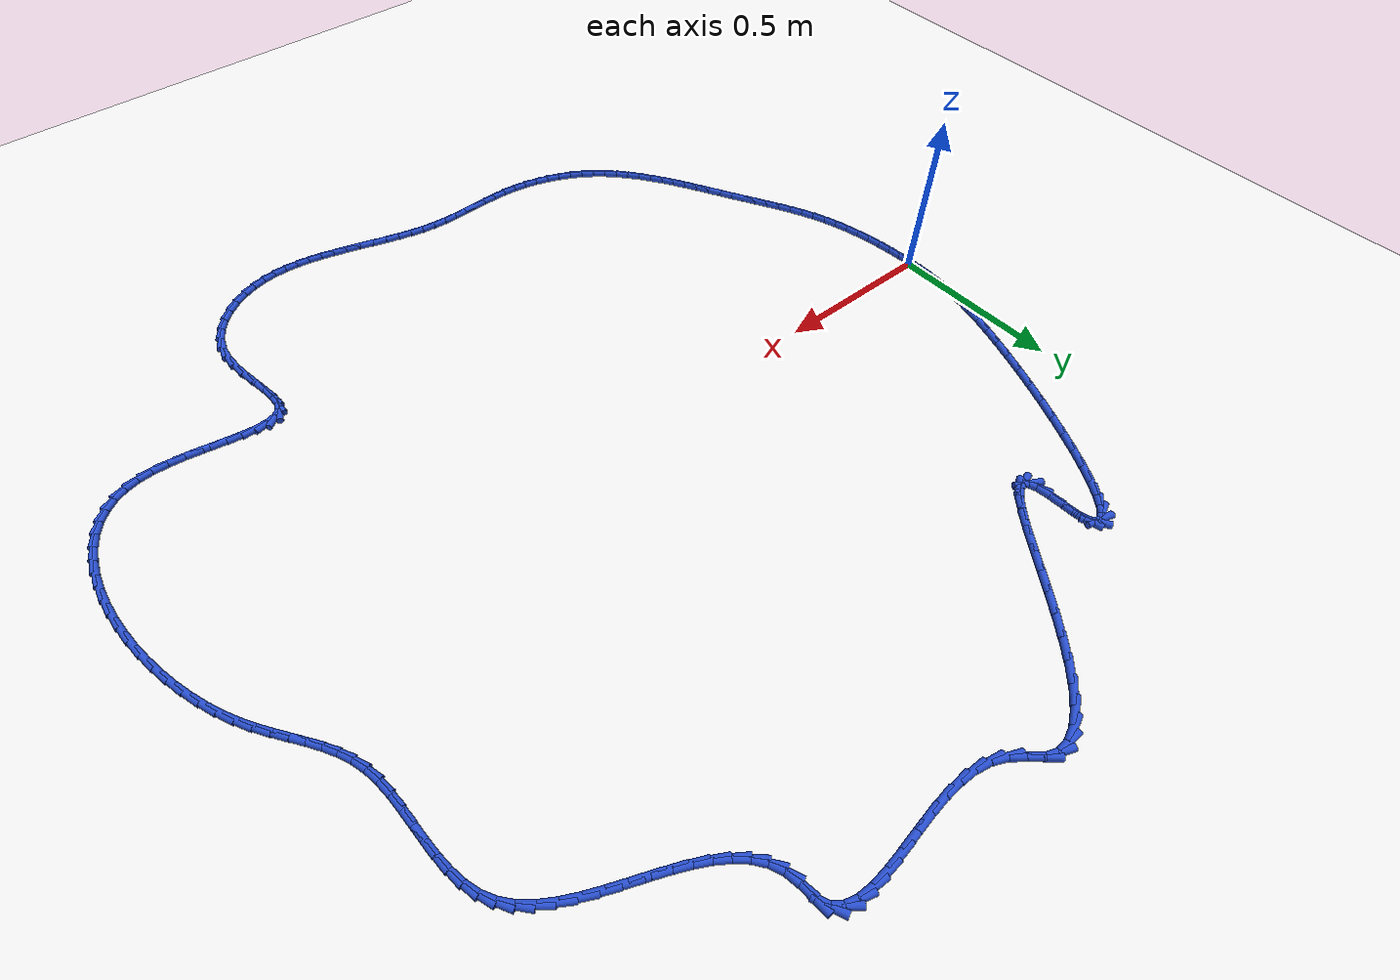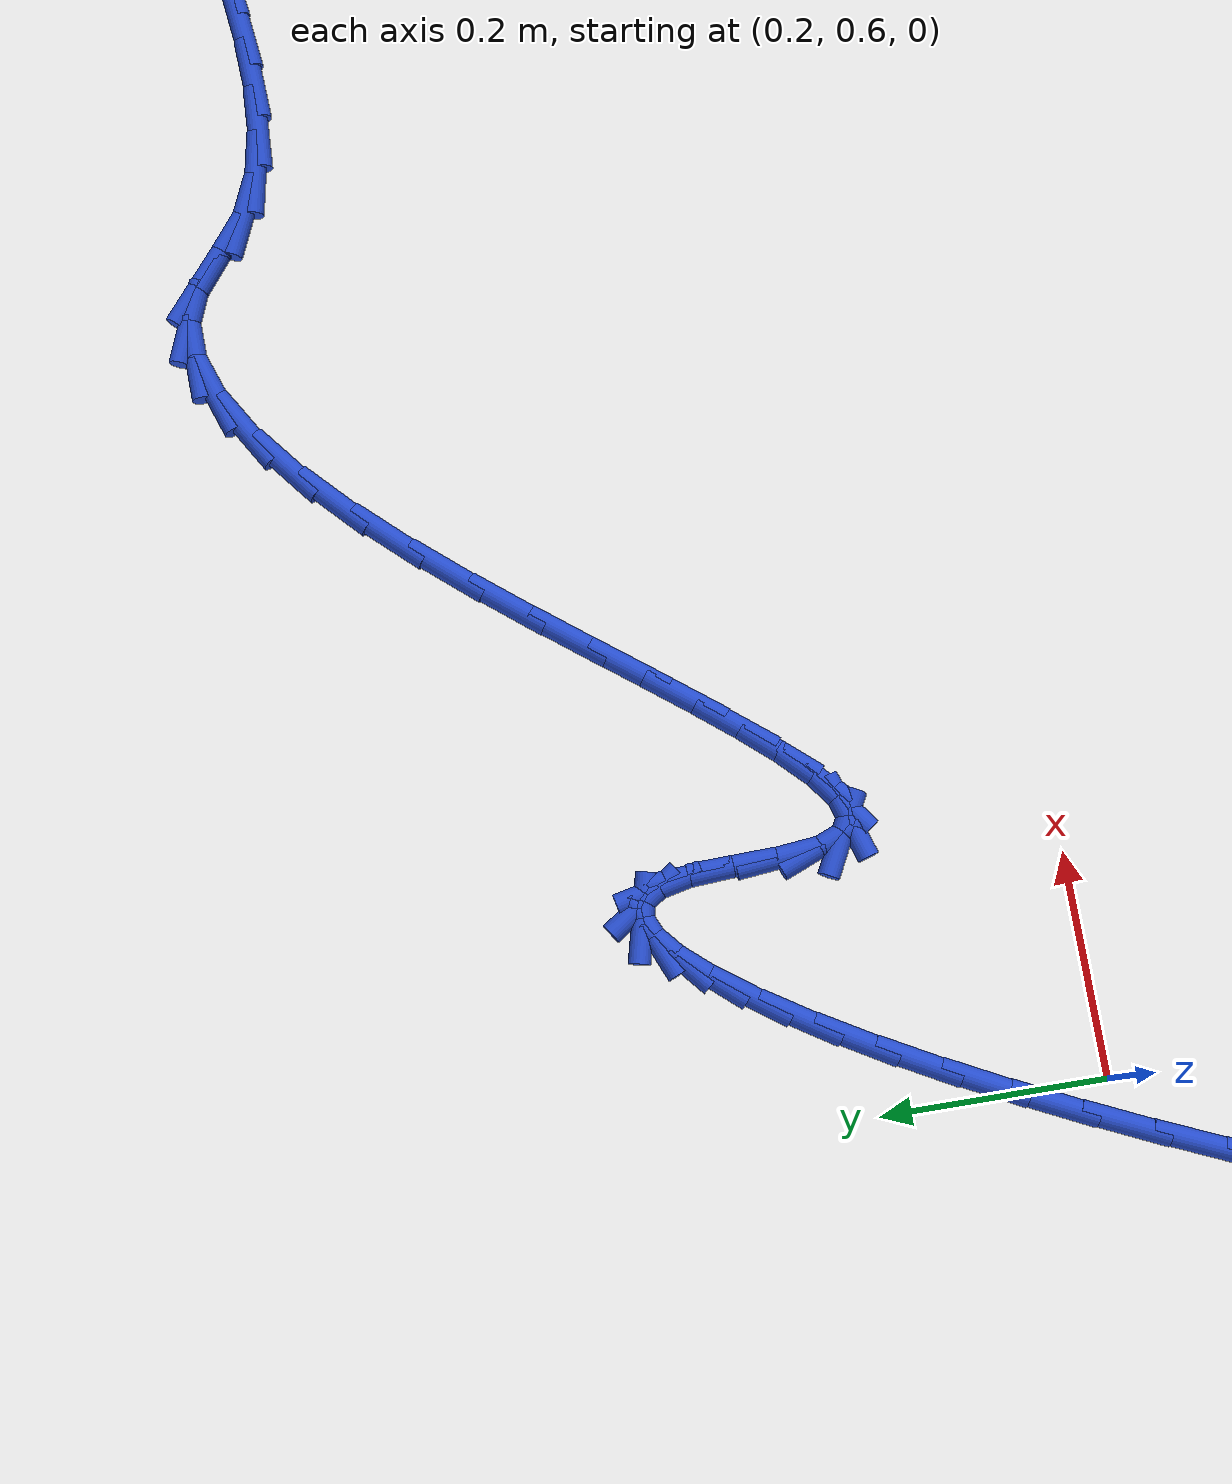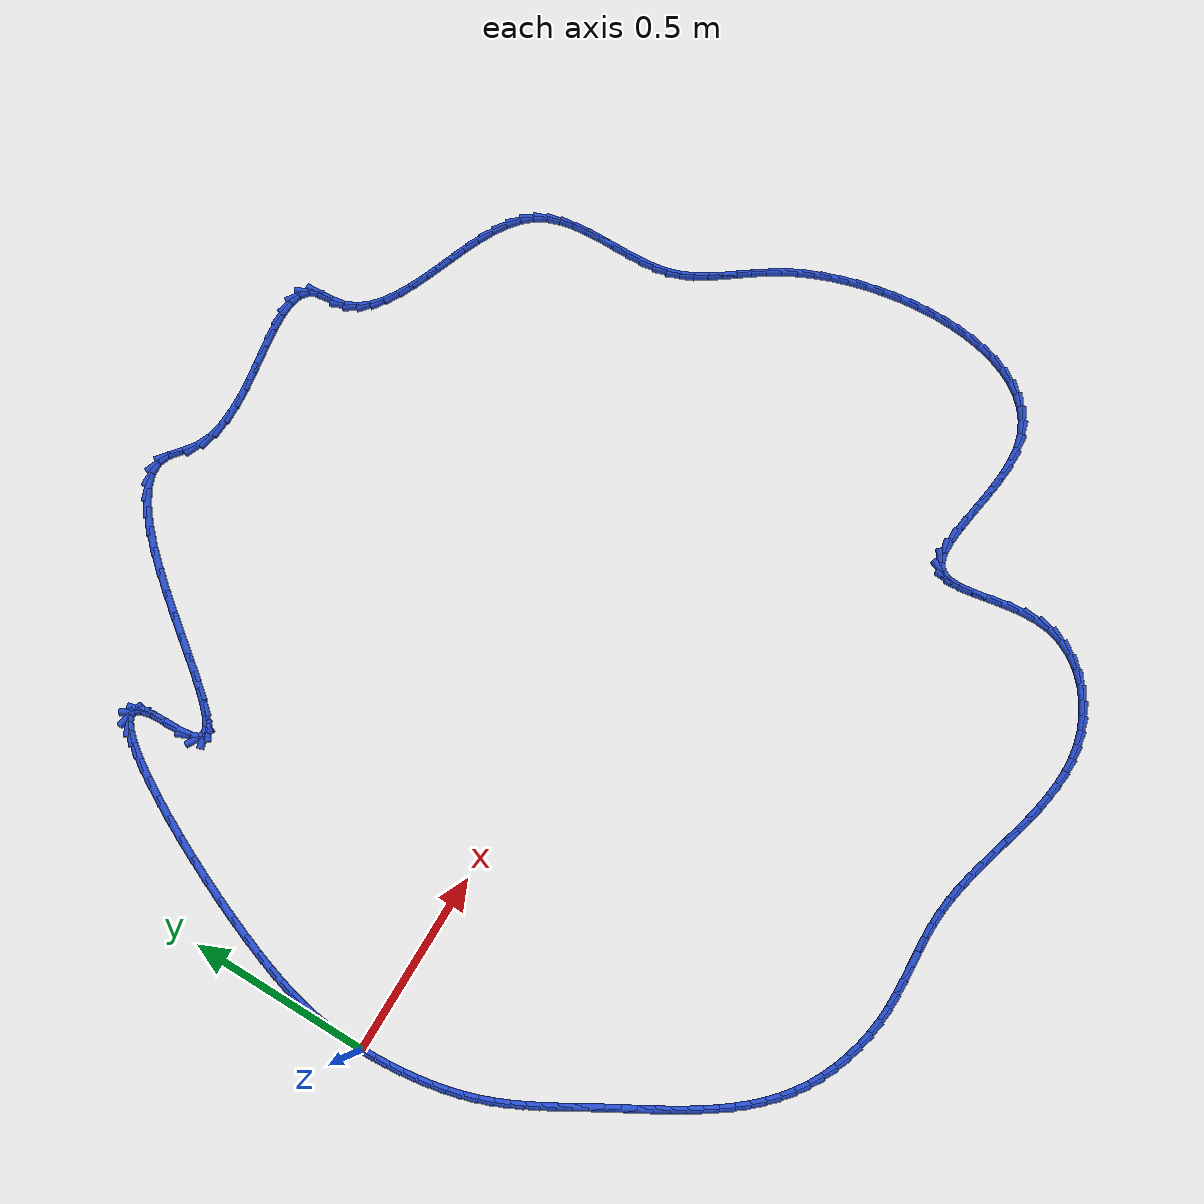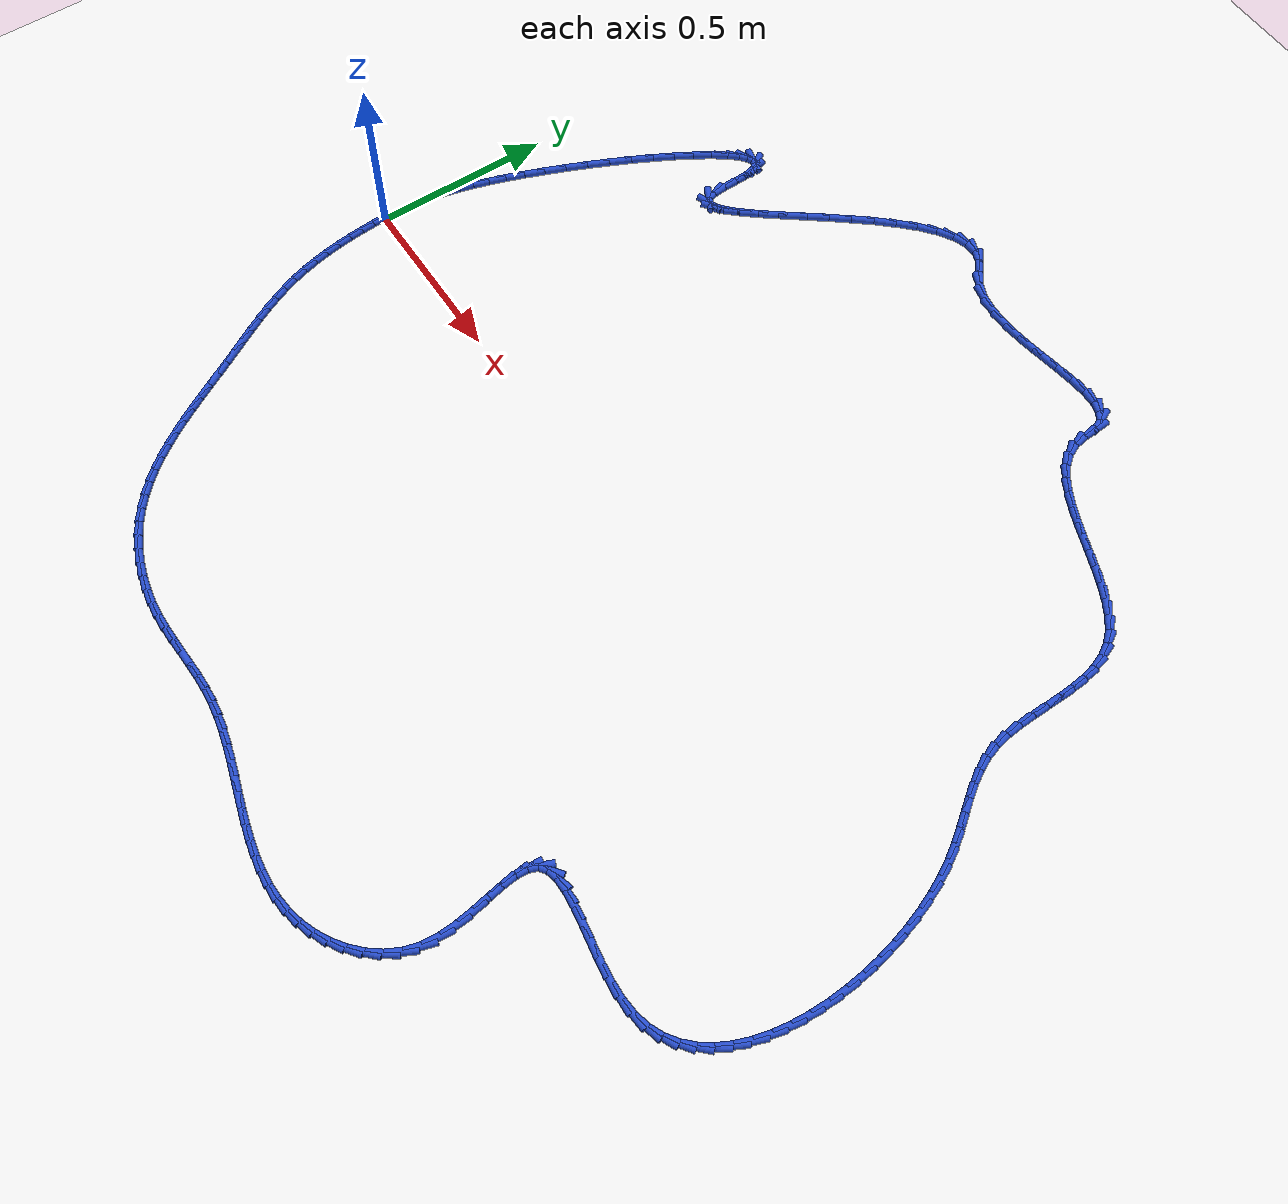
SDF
<sdf version="1.6">
 <world name="default">
  <light name="sun" type="directional">
   <pose>0 0 10 0 -0 0</pose>
   <diffuse>0.8 0.8 0.8 1</diffuse>
   <specular>0.2 0.2 0.2 1</specular>
   <attenuation>
    <range>1000</range>
    <constant>0.9</constant>
    <linear>0.01</linear>
    <quadratic>0.001</quadratic>
   </attenuation>
   <direction>-0.5 0.1 -0.9</direction>
  </light>
  <model name="ground_plane">
   <static>1</static>
   <link name="link">
    <collision name="collision">
     <geometry><plane><normal>0 0 1</normal><size>100 100</size></plane></geometry>
     <surface><friction><ode><mu>100</mu><mu2>50</mu2></ode></friction></surface>
    </collision>
    <visual name="visual">
     <cast_shadows>0</cast_shadows>
     <geometry><plane><normal>0 0 1</normal><size>100 100</size></plane></geometry>
     <material>
      <script><uri>file://media/materials/scripts/gazebo.material</uri><name>Gazebo/WhiteGlow</name></script>
     </material>
    </visual>
   </link>
  </model>
  <gravity>0 0 -9.8</gravity>
  <magnetic_field>6e-06 2.3e-05 -4.2e-05</magnetic_field>
  <atmosphere type="adiabatic"/>
  <physics name="default_physics" default="0" type="ode">
   <max_step_size>0.001</max_step_size>
   <real_time_factor>1</real_time_factor>
   <real_time_update_rate>1000</real_time_update_rate>
  </physics>
  <scene><ambient>0.4 0.4 0.4 1</ambient><background>0.7 0.7 0.7 1</background><shadows>1</shadows></scene>
  <spherical_coordinates>
   <surface_model>EARTH_WGS84</surface_model>
   <latitude_deg>0</latitude_deg>
   <longitude_deg>0</longitude_deg>
   <elevation>0</elevation>
   <heading_deg>0</heading_deg>
  </spherical_coordinates>
  <model name="line">
   <link name="link_0">
    <pose>1.1709383462843448e-17 -2.0816681711721685e-17 0.01 0 1.57 -1.568764740922635</pose>
    <collision name="collision">
     <geometry><cylinder><radius>0.01</radius><length>0.08</length></cylinder></geometry>
    </collision>
    <visual name="visual">
     <material>
      <script><name>Gazebo/Blue</name><uri>file://media/materials/scripts/gazebo.material</uri></script>
     </material>
     <geometry><cylinder><radius>0.01</radius><length>0.08</length></cylinder></geometry>
    </visual>
   </link>
   <link name="link_1">
    <pose>-7.468282264461221e-05 0.03676079899802648 0.01 0 1.57 1.5355054508221713</pose>
    <collision name="collision">
     <geometry><cylinder><radius>0.01</radius><length>0.08</length></cylinder></geometry>
    </collision>
    <visual name="visual">
     <material>
      <script><name>Gazebo/Blue</name><uri>file://media/materials/scripts/gazebo.material</uri></script>
     </material>
     <geometry><cylinder><radius>0.01</radius><length>0.08</length></cylinder></geometry>
    </visual>
   </link>
   <link name="link_2">
    <pose>0.0012002372762436623 0.07287185429100888 0.01 0 1.57 1.4914945790998744</pose>
    <collision name="collision">
     <geometry><cylinder><radius>0.01</radius><length>0.08</length></cylinder></geometry>
    </collision>
    <visual name="visual">
     <material>
      <script><name>Gazebo/Blue</name><uri>file://media/materials/scripts/gazebo.material</uri></script>
     </material>
     <geometry><cylinder><radius>0.01</radius><length>0.08</length></cylinder></geometry>
    </visual>
   </link>
   <link name="link_3">
    <pose>0.004075231434574496 0.1090496812685904 0.01 0 1.57 1.4436345479059882</pose>
    <collision name="collision">
     <geometry><cylinder><radius>0.01</radius><length>0.08</length></cylinder></geometry>
    </collision>
    <visual name="visual">
     <material>
      <script><name>Gazebo/Blue</name><uri>file://media/materials/scripts/gazebo.material</uri></script>
     </material>
     <geometry><cylinder><radius>0.01</radius><length>0.08</length></cylinder></geometry>
    </visual>
   </link>
   <link name="link_4">
    <pose>0.008800770790257555 0.1460107953204142 0.01 0 1.57 1.3951324595989985</pose>
    <collision name="collision">
     <geometry><cylinder><radius>0.01</radius><length>0.08</length></cylinder></geometry>
    </collision>
    <visual name="visual">
     <material>
      <script><name>Gazebo/Blue</name><uri>file://media/materials/scripts/gazebo.material</uri></script>
     </material>
     <geometry><cylinder><radius>0.01</radius><length>0.08</length></cylinder></geometry>
    </visual>
   </link>
   <link name="link_5">
    <pose>0.015627326481202505 0.18447171183612354 0.01 0 1.57 1.3488814153215</pose>
    <collision name="collision">
     <geometry><cylinder><radius>0.01</radius><length>0.08</length></cylinder></geometry>
    </collision>
    <visual name="visual">
     <material>
      <script><name>Gazebo/Blue</name><uri>file://media/materials/scripts/gazebo.material</uri></script>
     </material>
     <geometry><cylinder><radius>0.01</radius><length>0.08</length></cylinder></geometry>
    </visual>
   </link>
   <link name="link_6">
    <pose>0.024805369645319007 0.22514894620536158 0.01 0 1.57 1.3069715740940149</pose>
    <collision name="collision">
     <geometry><cylinder><radius>0.01</radius><length>0.08</length></cylinder></geometry>
    </collision>
    <visual name="visual">
     <material>
      <script><name>Gazebo/Blue</name><uri>file://media/materials/scripts/gazebo.material</uri></script>
     </material>
     <geometry><cylinder><radius>0.01</radius><length>0.08</length></cylinder></geometry>
    </visual>
   </link>
   <link name="link_7">
    <pose>0.03658537142051675 0.2687590138177717 0.01 0 1.57 1.270539225523364</pose>
    <collision name="collision">
     <geometry><cylinder><radius>0.01</radius><length>0.08</length></cylinder></geometry>
    </collision>
    <visual name="visual">
     <material>
      <script><name>Gazebo/Blue</name><uri>file://media/materials/scripts/gazebo.material</uri></script>
     </material>
     <geometry><cylinder><radius>0.01</radius><length>0.08</length></cylinder></geometry>
    </visual>
   </link>
   <link name="link_8">
    <pose>0.051217482449885235 0.3160176105698323 0.01 0 1.57 1.2402362665513227</pose>
    <collision name="collision">
     <geometry><cylinder><radius>0.01</radius><length>0.08</length></cylinder></geometry>
    </collision>
    <visual name="visual">
     <material>
      <script><name>Gazebo/Blue</name><uri>file://media/materials/scripts/gazebo.material</uri></script>
     </material>
     <geometry><cylinder><radius>0.01</radius><length>0.08</length></cylinder></geometry>
    </visual>
   </link>
   <link name="link_9">
    <pose>0.06878901132593096 0.36722405137787556 0.01 0 1.57 1.2154882764751367</pose>
    <collision name="collision">
     <geometry><cylinder><radius>0.01</radius><length>0.08</length></cylinder></geometry>
    </collision>
    <visual name="visual">
     <material>
      <script><name>Gazebo/Blue</name><uri>file://media/materials/scripts/gazebo.material</uri></script>
     </material>
     <geometry><cylinder><radius>0.01</radius><length>0.08</length></cylinder></geometry>
    </visual>
   </link>
   <link name="link_10">
    <pose>0.0889599540403434 0.42158502895825334 0.01 0 1.57 1.1942134926526518</pose>
    <collision name="collision">
     <geometry><cylinder><radius>0.01</radius><length>0.08</length></cylinder></geometry>
    </collision>
    <visual name="visual">
     <material>
      <script><name>Gazebo/Blue</name><uri>file://media/materials/scripts/gazebo.material</uri></script>
     </material>
     <geometry><cylinder><radius>0.01</radius><length>0.08</length></cylinder></geometry>
    </visual>
   </link>
   <link name="link_11">
    <pose>0.11132106244470293 0.4781301813732841 0.01 0 1.57 1.1748876541137376</pose>
    <collision name="collision">
     <geometry><cylinder><radius>0.01</radius><length>0.08</length></cylinder></geometry>
    </collision>
    <visual name="visual">
     <material>
      <script><name>Gazebo/Blue</name><uri>file://media/materials/scripts/gazebo.material</uri></script>
     </material>
     <geometry><cylinder><radius>0.01</radius><length>0.08</length></cylinder></geometry>
    </visual>
   </link>
   <link name="link_12">
    <pose>0.13546308839059001 0.5358891466852866 0.01 0 1.57 1.1563958798590623</pose>
    <collision name="collision">
     <geometry><cylinder><radius>0.01</radius><length>0.08</length></cylinder></geometry>
    </collision>
    <visual name="visual">
     <material>
      <script><name>Gazebo/Blue</name><uri>file://media/materials/scripts/gazebo.material</uri></script>
     </material>
     <geometry><cylinder><radius>0.01</radius><length>0.08</length></cylinder></geometry>
    </visual>
   </link>
   <link name="link_13">
    <pose>0.16097678372958496 0.5938915629565795 0.01 0 1.57 1.1377947267360347</pose>
    <collision name="collision">
     <geometry><cylinder><radius>0.01</radius><length>0.08</length></cylinder></geometry>
    </collision>
    <visual name="visual">
     <material>
      <script><name>Gazebo/Blue</name><uri>file://media/materials/scripts/gazebo.material</uri></script>
     </material>
     <geometry><cylinder><radius>0.01</radius><length>0.08</length></cylinder></geometry>
    </visual>
   </link>
   <link name="link_14">
    <pose>0.18745290031326825 0.6511670682494815 0.01 0 1.57 1.1181454501736163</pose>
    <collision name="collision">
     <geometry><cylinder><radius>0.01</radius><length>0.08</length></cylinder></geometry>
    </collision>
    <visual name="visual">
     <material>
      <script><name>Gazebo/Blue</name><uri>file://media/materials/scripts/gazebo.material</uri></script>
     </material>
     <geometry><cylinder><radius>0.01</radius><length>0.08</length></cylinder></geometry>
    </visual>
   </link>
   <link name="link_15">
    <pose>0.2144821899932202 0.7067453006263108 0.01 0 1.57 1.0963529561204812</pose>
    <collision name="collision">
     <geometry><cylinder><radius>0.01</radius><length>0.08</length></cylinder></geometry>
    </collision>
    <visual name="visual">
     <material>
      <script><name>Gazebo/Blue</name><uri>file://media/materials/scripts/gazebo.material</uri></script>
     </material>
     <geometry><cylinder><radius>0.01</radius><length>0.08</length></cylinder></geometry>
    </visual>
   </link>
   <link name="link_16">
    <pose>0.24165540462102134 0.7596558981493867 0.01 0 1.57 1.0709503467464274</pose>
    <collision name="collision">
     <geometry><cylinder><radius>0.01</radius><length>0.08</length></cylinder></geometry>
    </collision>
    <visual name="visual">
     <material>
      <script><name>Gazebo/Blue</name><uri>file://media/materials/scripts/gazebo.material</uri></script>
     </material>
     <geometry><cylinder><radius>0.01</radius><length>0.08</length></cylinder></geometry>
    </visual>
   </link>
   <link name="link_17">
    <pose>0.26856329604825185 0.8089284988810272 0.01 0 1.57 1.039733929315308</pose>
    <collision name="collision">
     <geometry><cylinder><radius>0.01</radius><length>0.08</length></cylinder></geometry>
    </collision>
    <visual name="visual">
     <material>
      <script><name>Gazebo/Blue</name><uri>file://media/materials/scripts/gazebo.material</uri></script>
     </material>
     <geometry><cylinder><radius>0.01</radius><length>0.08</length></cylinder></geometry>
    </visual>
   </link>
   <link name="link_18">
    <pose>0.2947966161264923 0.8535927408835512 0.01 0 1.57 0.9990408790225557</pose>
    <collision name="collision">
     <geometry><cylinder><radius>0.01</radius><length>0.08</length></cylinder></geometry>
    </collision>
    <visual name="visual">
     <material>
      <script><name>Gazebo/Blue</name><uri>file://media/materials/scripts/gazebo.material</uri></script>
     </material>
     <geometry><cylinder><radius>0.01</radius><length>0.08</length></cylinder></geometry>
    </visual>
   </link>
   <link name="link_19">
    <pose>0.319946116707323 0.8926782622192776 0.01 0 1.57 0.9421293417932</pose>
    <collision name="collision">
     <geometry><cylinder><radius>0.01</radius><length>0.08</length></cylinder></geometry>
    </collision>
    <visual name="visual">
     <material>
      <script><name>Gazebo/Blue</name><uri>file://media/materials/scripts/gazebo.material</uri></script>
     </material>
     <geometry><cylinder><radius>0.01</radius><length>0.08</length></cylinder></geometry>
    </visual>
   </link>
   <link name="link_20">
    <pose>0.3436025496423244 0.9252147009505244 0.01 0 1.57 0.8550479765291604</pose>
    <collision name="collision">
     <geometry><cylinder><radius>0.01</radius><length>0.08</length></cylinder></geometry>
    </collision>
    <visual name="visual">
     <material>
      <script><name>Gazebo/Blue</name><uri>file://media/materials/scripts/gazebo.material</uri></script>
     </material>
     <geometry><cylinder><radius>0.01</radius><length>0.08</length></cylinder></geometry>
    </visual>
   </link>
   <link name="link_21">
    <pose>0.36535666678307677 0.9502316951396105 0.01 0 1.57 0.7045244455720923</pose>
    <collision name="collision">
     <geometry><cylinder><radius>0.01</radius><length>0.08</length></cylinder></geometry>
    </collision>
    <visual name="visual">
     <material>
      <script><name>Gazebo/Blue</name><uri>file://media/materials/scripts/gazebo.material</uri></script>
     </material>
     <geometry><cylinder><radius>0.01</radius><length>0.08</length></cylinder></geometry>
    </visual>
   </link>
   <link name="link_22">
    <pose>0.38479921998116073 0.9667588828488549 0.01 0 1.57 0.39985695043769515</pose>
    <collision name="collision">
     <geometry><cylinder><radius>0.01</radius><length>0.08</length></cylinder></geometry>
    </collision>
    <visual name="visual">
     <material>
      <script><name>Gazebo/Blue</name><uri>file://media/materials/scripts/gazebo.material</uri></script>
     </material>
     <geometry><cylinder><radius>0.01</radius><length>0.08</length></cylinder></geometry>
    </visual>
   </link>
   <link name="link_23">
    <pose>0.4015209610881564 0.9738259021405755 0.01 0 1.57 -0.2425945336687161</pose>
    <collision name="collision">
     <geometry><cylinder><radius>0.01</radius><length>0.08</length></cylinder></geometry>
    </collision>
    <visual name="visual">
     <material>
      <script><name>Gazebo/Blue</name><uri>file://media/materials/scripts/gazebo.material</uri></script>
     </material>
     <geometry><cylinder><radius>0.01</radius><length>0.08</length></cylinder></geometry>
    </visual>
   </link>
   <link name="link_24">
    <pose>0.4151126419556447 0.9704623910770924 0.01 0 1.57 -0.973037345270926</pose>
    <collision name="collision">
     <geometry><cylinder><radius>0.01</radius><length>0.08</length></cylinder></geometry>
    </collision>
    <visual name="visual">
     <material>
      <script><name>Gazebo/Blue</name><uri>file://media/materials/scripts/gazebo.material</uri></script>
     </material>
     <geometry><cylinder><radius>0.01</radius><length>0.08</length></cylinder></geometry>
    </visual>
   </link>
   <link name="link_25">
    <pose>0.4251650144352053 0.9556979877207223 0.01 0 1.57 -1.3495417607274645</pose>
    <collision name="collision">
     <geometry><cylinder><radius>0.01</radius><length>0.08</length></cylinder></geometry>
    </collision>
    <visual name="visual">
     <material>
      <script><name>Gazebo/Blue</name><uri>file://media/materials/scripts/gazebo.material</uri></script>
     </material>
     <geometry><cylinder><radius>0.01</radius><length>0.08</length></cylinder></geometry>
    </visual>
   </link>
   <link name="link_26">
    <pose>0.431268830378419 0.9285623301337849 0.01 0 1.57 -1.5131103198542823</pose>
    <collision name="collision">
     <geometry><cylinder><radius>0.01</radius><length>0.08</length></cylinder></geometry>
    </collision>
    <visual name="visual">
     <material>
      <script><name>Gazebo/Blue</name><uri>file://media/materials/scripts/gazebo.material</uri></script>
     </material>
     <geometry><cylinder><radius>0.01</radius><length>0.08</length></cylinder></geometry>
    </visual>
   </link>
   <link name="link_27">
    <pose>0.43352125430816163 0.8895593717146986 0.01 0 1.57 -1.54504843713999</pose>
    <collision name="collision">
     <geometry><cylinder><radius>0.01</radius><length>0.08</length></cylinder></geometry>
    </collision>
    <visual name="visual">
     <material>
      <script><name>Gazebo/Blue</name><uri>file://media/materials/scripts/gazebo.material</uri></script>
     </material>
     <geometry><cylinder><radius>0.01</radius><length>0.08</length></cylinder></geometry>
    </visual>
   </link>
   <link name="link_28">
    <pose>0.4346231514541276 0.846773199812439 0.01 0 1.57 -1.4744182706913913</pose>
    <collision name="collision">
     <geometry><cylinder><radius>0.01</radius><length>0.08</length></cylinder></geometry>
    </collision>
    <visual name="visual">
     <material>
      <script><name>Gazebo/Blue</name><uri>file://media/materials/scripts/gazebo.material</uri></script>
     </material>
     <geometry><cylinder><radius>0.01</radius><length>0.08</length></cylinder></geometry>
    </visual>
   </link>
   <link name="link_29">
    <pose>0.4381091562238803 0.8107151519353102 0.01 0 1.57 -1.1935511905397567</pose>
    <collision name="collision">
     <geometry><cylinder><radius>0.01</radius><length>0.08</length></cylinder></geometry>
    </collision>
    <visual name="visual">
     <material>
      <script><name>Gazebo/Blue</name><uri>file://media/materials/scripts/gazebo.material</uri></script>
     </material>
     <geometry><cylinder><radius>0.01</radius><length>0.08</length></cylinder></geometry>
    </visual>
   </link>
   <link name="link_30">
    <pose>0.44663193816883195 0.7892050272643987 0.01 0 1.57 -0.48249954833357417</pose>
    <collision name="collision">
     <geometry><cylinder><radius>0.01</radius><length>0.08</length></cylinder></geometry>
    </collision>
    <visual name="visual">
     <material>
      <script><name>Gazebo/Blue</name><uri>file://media/materials/scripts/gazebo.material</uri></script>
     </material>
     <geometry><cylinder><radius>0.01</radius><length>0.08</length></cylinder></geometry>
    </visual>
   </link>
   <link name="link_31">
    <pose>0.46022929452914607 0.7820828407072101 0.01 0 1.57 0.29980054642361725</pose>
    <collision name="collision">
     <geometry><cylinder><radius>0.01</radius><length>0.08</length></cylinder></geometry>
    </collision>
    <visual name="visual">
     <material>
      <script><name>Gazebo/Blue</name><uri>file://media/materials/scripts/gazebo.material</uri></script>
     </material>
     <geometry><cylinder><radius>0.01</radius><length>0.08</length></cylinder></geometry>
    </visual>
   </link>
   <link name="link_32">
    <pose>0.47845689958031923 0.7877173164949023 0.01 0 1.57 0.6420637533860102</pose>
    <collision name="collision">
     <geometry><cylinder><radius>0.01</radius><length>0.08</length></cylinder></geometry>
    </collision>
    <visual name="visual">
     <material>
      <script><name>Gazebo/Blue</name><uri>file://media/materials/scripts/gazebo.material</uri></script>
     </material>
     <geometry><cylinder><radius>0.01</radius><length>0.08</length></cylinder></geometry>
    </visual>
   </link>
   <link name="link_33">
    <pose>0.5008704275978486 0.8044771788586335 0.01 0 1.57 0.7872842441982141</pose>
    <collision name="collision">
     <geometry><cylinder><radius>0.01</radius><length>0.08</length></cylinder></geometry>
    </collision>
    <visual name="visual">
     <material>
      <script><name>Gazebo/Blue</name><uri>file://media/materials/scripts/gazebo.material</uri></script>
     </material>
     <geometry><cylinder><radius>0.01</radius><length>0.08</length></cylinder></geometry>
    </visual>
   </link>
   <link name="link_34">
    <pose>0.5270255528572307 0.830731152029561 0.01 0 1.57 0.8586422349914501</pose>
    <collision name="collision">
     <geometry><cylinder><radius>0.01</radius><length>0.08</length></cylinder></geometry>
    </collision>
    <visual name="visual">
     <material>
      <script><name>Gazebo/Blue</name><uri>file://media/materials/scripts/gazebo.material</uri></script>
     </material>
     <geometry><cylinder><radius>0.01</radius><length>0.08</length></cylinder></geometry>
    </visual>
   </link>
   <link name="link_35">
    <pose>0.5564779496339628 0.8648479602388438 0.01 0 1.57 0.8956527932185162</pose>
    <collision name="collision">
     <geometry><cylinder><radius>0.01</radius><length>0.08</length></cylinder></geometry>
    </collision>
    <visual name="visual">
     <material>
      <script><name>Gazebo/Blue</name><uri>file://media/materials/scripts/gazebo.material</uri></script>
     </material>
     <geometry><cylinder><radius>0.01</radius><length>0.08</length></cylinder></geometry>
    </visual>
   </link>
   <link name="link_36">
    <pose>0.5887832922035409 0.9051963277176385 0.01 0 1.57 0.9131736409051385</pose>
    <collision name="collision">
     <geometry><cylinder><radius>0.01</radius><length>0.08</length></cylinder></geometry>
    </collision>
    <visual name="visual">
     <material>
      <script><name>Gazebo/Blue</name><uri>file://media/materials/scripts/gazebo.material</uri></script>
     </material>
     <geometry><cylinder><radius>0.01</radius><length>0.08</length></cylinder></geometry>
    </visual>
   </link>
   <link name="link_37">
    <pose>0.6234972548414629 0.9501449786971046 0.01 0 1.57 0.9174844662995174</pose>
    <collision name="collision">
     <geometry><cylinder><radius>0.01</radius><length>0.08</length></cylinder></geometry>
    </collision>
    <visual name="visual">
     <material>
      <script><name>Gazebo/Blue</name><uri>file://media/materials/scripts/gazebo.material</uri></script>
     </material>
     <geometry><cylinder><radius>0.01</radius><length>0.08</length></cylinder></geometry>
    </visual>
   </link>
   <link name="link_38">
    <pose>0.6601755118232249 0.9980626374083987 0.01 0 1.57 0.9111654602945956</pose>
    <collision name="collision">
     <geometry><cylinder><radius>0.01</radius><length>0.08</length></cylinder></geometry>
    </collision>
    <visual name="visual">
     <material>
      <script><name>Gazebo/Blue</name><uri>file://media/materials/scripts/gazebo.material</uri></script>
     </material>
     <geometry><cylinder><radius>0.01</radius><length>0.08</length></cylinder></geometry>
    </visual>
   </link>
   <link name="link_39">
    <pose>0.6983737374243241 1.0473180280826797 0.01 0 1.57 0.8947566819144622</pose>
    <collision name="collision">
     <geometry><cylinder><radius>0.01</radius><length>0.08</length></cylinder></geometry>
    </collision>
    <visual name="visual">
     <material>
      <script><name>Gazebo/Blue</name><uri>file://media/materials/scripts/gazebo.material</uri></script>
     </material>
     <geometry><cylinder><radius>0.01</radius><length>0.08</length></cylinder></geometry>
    </visual>
   </link>
   <link name="link_40">
    <pose>0.7376476059202572 1.0962798749511051 0.01 0 1.57 0.8672445904938844</pose>
    <collision name="collision">
     <geometry><cylinder><radius>0.01</radius><length>0.08</length></cylinder></geometry>
    </collision>
    <visual name="visual">
     <material>
      <script><name>Gazebo/Blue</name><uri>file://media/materials/scripts/gazebo.material</uri></script>
     </material>
     <geometry><cylinder><radius>0.01</radius><length>0.08</length></cylinder></geometry>
    </visual>
   </link>
   <link name="link_41">
    <pose>0.7775527915865211 1.1433169022448335 0.01 0 1.57 0.8259243502828172</pose>
    <collision name="collision">
     <geometry><cylinder><radius>0.01</radius><length>0.08</length></cylinder></geometry>
    </collision>
    <visual name="visual">
     <material>
      <script><name>Gazebo/Blue</name><uri>file://media/materials/scripts/gazebo.material</uri></script>
     </material>
     <geometry><cylinder><radius>0.01</radius><length>0.08</length></cylinder></geometry>
    </visual>
   </link>
   <link name="link_42">
    <pose>0.8176449686986123 1.1867978341950216 0.01 0 1.57 0.7656731718907847</pose>
    <collision name="collision">
     <geometry><cylinder><radius>0.01</radius><length>0.08</length></cylinder></geometry>
    </collision>
    <visual name="visual">
     <material>
      <script><name>Gazebo/Blue</name><uri>file://media/materials/scripts/gazebo.material</uri></script>
     </material>
     <geometry><cylinder><radius>0.01</radius><length>0.08</length></cylinder></geometry>
    </visual>
   </link>
   <link name="link_43">
    <pose>0.8574798115320279 1.2250913950328284 0.01 0 1.57 0.6773588734244219</pose>
    <collision name="collision">
     <geometry><cylinder><radius>0.01</radius><length>0.08</length></cylinder></geometry>
    </collision>
    <visual name="visual">
     <material>
      <script><name>Gazebo/Blue</name><uri>file://media/materials/scripts/gazebo.material</uri></script>
     </material>
     <geometry><cylinder><radius>0.01</radius><length>0.08</length></cylinder></geometry>
    </visual>
   </link>
   <link name="link_44">
    <pose>0.8966129943622647 1.2565663089894115 0.01 0 1.57 0.5449110376335393</pose>
    <collision name="collision">
     <geometry><cylinder><radius>0.01</radius><length>0.08</length></cylinder></geometry>
    </collision>
    <visual name="visual">
     <material>
      <script><name>Gazebo/Blue</name><uri>file://media/materials/scripts/gazebo.material</uri></script>
     </material>
     <geometry><cylinder><radius>0.01</radius><length>0.08</length></cylinder></geometry>
    </visual>
   </link>
   <link name="link_45">
    <pose>0.9346001914648198 1.2795913002959292 0.01 0 1.57 0.3416808088666626</pose>
    <collision name="collision">
     <geometry><cylinder><radius>0.01</radius><length>0.08</length></cylinder></geometry>
    </collision>
    <visual name="visual">
     <material>
      <script><name>Gazebo/Blue</name><uri>file://media/materials/scripts/gazebo.material</uri></script>
     </material>
     <geometry><cylinder><radius>0.01</radius><length>0.08</length></cylinder></geometry>
    </visual>
   </link>
   <link name="link_46">
    <pose>0.97099707711519 1.2925350931835393 0.01 0 1.57 0.035818147539107156</pose>
    <collision name="collision">
     <geometry><cylinder><radius>0.01</radius><length>0.08</length></cylinder></geometry>
    </collision>
    <visual name="visual">
     <material>
      <script><name>Gazebo/Blue</name><uri>file://media/materials/scripts/gazebo.material</uri></script>
     </material>
     <geometry><cylinder><radius>0.01</radius><length>0.08</length></cylinder></geometry>
    </visual>
   </link>
   <link name="link_47">
    <pose>1.0053593255888715 1.2937664118833994 0.01 0 1.57 -0.36305883201565475</pose>
    <collision name="collision">
     <geometry><cylinder><radius>0.01</radius><length>0.08</length></cylinder></geometry>
    </collision>
    <visual name="visual">
     <material>
      <script><name>Gazebo/Blue</name><uri>file://media/materials/scripts/gazebo.material</uri></script>
     </material>
     <geometry><cylinder><radius>0.01</radius><length>0.08</length></cylinder></geometry>
    </visual>
   </link>
   <link name="link_48">
    <pose>1.0372426111613615 1.2816539806266678 0.01 0 1.57 -0.6841480375733638</pose>
    <collision name="collision">
     <geometry><cylinder><radius>0.01</radius><length>0.08</length></cylinder></geometry>
    </collision>
    <visual name="visual">
     <material>
      <script><name>Gazebo/Blue</name><uri>file://media/materials/scripts/gazebo.material</uri></script>
     </material>
     <geometry><cylinder><radius>0.01</radius><length>0.08</length></cylinder></geometry>
    </visual>
   </link>
   <link name="link_49">
    <pose>1.0672203175678752 1.2572058095918428 0.01 0 1.57 -0.6562181619540158</pose>
    <collision name="collision">
     <geometry><cylinder><radius>0.01</radius><length>0.08</length></cylinder></geometry>
    </collision>
    <visual name="visual">
     <material>
      <script><name>Gazebo/Blue</name><uri>file://media/materials/scripts/gazebo.material</uri></script>
     </material>
     <geometry><cylinder><radius>0.01</radius><length>0.08</length></cylinder></geometry>
    </visual>
   </link>
   <link name="link_50">
    <pose>1.0999426403726085 1.2320075650167843 0.01 0 1.57 -0.40077037514675196</pose>
    <collision name="collision">
     <geometry><cylinder><radius>0.01</radius><length>0.08</length></cylinder></geometry>
    </collision>
    <visual name="visual">
     <material>
      <script><name>Gazebo/Blue</name><uri>file://media/materials/scripts/gazebo.material</uri></script>
     </material>
     <geometry><cylinder><radius>0.01</radius><length>0.08</length></cylinder></geometry>
    </visual>
   </link>
   <link name="link_51">
    <pose>1.1389421458291702 1.2154834122471758 0.01 0 1.57 -0.18464626799693962</pose>
    <collision name="collision">
     <geometry><cylinder><radius>0.01</radius><length>0.08</length></cylinder></geometry>
    </collision>
    <visual name="visual">
     <material>
      <script><name>Gazebo/Blue</name><uri>file://media/materials/scripts/gazebo.material</uri></script>
     </material>
     <geometry><cylinder><radius>0.01</radius><length>0.08</length></cylinder></geometry>
    </visual>
   </link>
   <link name="link_52">
    <pose>1.1833641389090774 1.20718655024264 0.01 0 1.57 -0.035540415858139815</pose>
    <collision name="collision">
     <geometry><cylinder><radius>0.01</radius><length>0.08</length></cylinder></geometry>
    </collision>
    <visual name="visual">
     <material>
      <script><name>Gazebo/Blue</name><uri>file://media/materials/scripts/gazebo.material</uri></script>
     </material>
     <geometry><cylinder><radius>0.01</radius><length>0.08</length></cylinder></geometry>
    </visual>
   </link>
   <link name="link_53">
    <pose>1.231817720588235 1.2054637643764308 0.01 0 1.57 0.06251012044511524</pose>
    <collision name="collision">
     <geometry><cylinder><radius>0.01</radius><length>0.08</length></cylinder></geometry>
    </collision>
    <visual name="visual">
     <material>
      <script><name>Gazebo/Blue</name><uri>file://media/materials/scripts/gazebo.material</uri></script>
     </material>
     <geometry><cylinder><radius>0.01</radius><length>0.08</length></cylinder></geometry>
    </visual>
   </link>
   <link name="link_54">
    <pose>1.2829119918425473 1.2086618400218037 0.01 0 1.57 0.12290096199764607</pose>
    <collision name="collision">
     <geometry><cylinder><radius>0.01</radius><length>0.08</length></cylinder></geometry>
    </collision>
    <visual name="visual">
     <material>
      <script><name>Gazebo/Blue</name><uri>file://media/materials/scripts/gazebo.material</uri></script>
     </material>
     <geometry><cylinder><radius>0.01</radius><length>0.08</length></cylinder></geometry>
    </visual>
   </link>
   <link name="link_55">
    <pose>1.33525605364792 1.215127562552015 0.01 0 1.57 0.15356485314063414</pose>
    <collision name="collision">
     <geometry><cylinder><radius>0.01</radius><length>0.08</length></cylinder></geometry>
    </collision>
    <visual name="visual">
     <material>
      <script><name>Gazebo/Blue</name><uri>file://media/materials/scripts/gazebo.material</uri></script>
     </material>
     <geometry><cylinder><radius>0.01</radius><length>0.08</length></cylinder></geometry>
    </visual>
   </link>
   <link name="link_56">
    <pose>1.3874590069802577 1.223207717340319 0.01 0 1.57 0.15738540133013484</pose>
    <collision name="collision">
     <geometry><cylinder><radius>0.01</radius><length>0.08</length></cylinder></geometry>
    </collision>
    <visual name="visual">
     <material>
      <script><name>Gazebo/Blue</name><uri>file://media/materials/scripts/gazebo.material</uri></script>
     </material>
     <geometry><cylinder><radius>0.01</radius><length>0.08</length></cylinder></geometry>
    </visual>
   </link>
   <link name="link_57">
    <pose>1.4381299528154652 1.2312490897599708 0.01 0 1.57 0.13220108576649578</pose>
    <collision name="collision">
     <geometry><cylinder><radius>0.01</radius><length>0.08</length></cylinder></geometry>
    </collision>
    <visual name="visual">
     <material>
      <script><name>Gazebo/Blue</name><uri>file://media/materials/scripts/gazebo.material</uri></script>
     </material>
     <geometry><cylinder><radius>0.01</radius><length>0.08</length></cylinder></geometry>
    </visual>
   </link>
   <link name="link_58">
    <pose>1.485877992129447 1.237598465184226 0.01 0 1.57 0.0690558275595702</pose>
    <collision name="collision">
     <geometry><cylinder><radius>0.01</radius><length>0.08</length></cylinder></geometry>
    </collision>
    <visual name="visual">
     <material>
      <script><name>Gazebo/Blue</name><uri>file://media/materials/scripts/gazebo.material</uri></script>
     </material>
     <geometry><cylinder><radius>0.01</radius><length>0.08</length></cylinder></geometry>
    </visual>
   </link>
   <link name="link_59">
    <pose>1.5293122258981091 1.2406026289863399 0.01 0 1.57 -0.05280766492518197</pose>
    <collision name="collision">
     <geometry><cylinder><radius>0.01</radius><length>0.08</length></cylinder></geometry>
    </collision>
    <visual name="visual">
     <material>
      <script><name>Gazebo/Blue</name><uri>file://media/materials/scripts/gazebo.material</uri></script>
     </material>
     <geometry><cylinder><radius>0.01</radius><length>0.08</length></cylinder></geometry>
    </visual>
   </link>
   <link name="link_60">
    <pose>1.5670417550973552 1.2386083665395677 0.01 0 1.57 -0.275078118105675</pose>
    <collision name="collision">
     <geometry><cylinder><radius>0.01</radius><length>0.08</length></cylinder></geometry>
    </collision>
    <visual name="visual">
     <material>
      <script><name>Gazebo/Blue</name><uri>file://media/materials/scripts/gazebo.material</uri></script>
     </material>
     <geometry><cylinder><radius>0.01</radius><length>0.08</length></cylinder></geometry>
    </visual>
   </link>
   <link name="link_61">
    <pose>1.5976756807030914 1.2299624632171642 0.01 0 1.57 -0.6532594559871524</pose>
    <collision name="collision">
     <geometry><cylinder><radius>0.01</radius><length>0.08</length></cylinder></geometry>
    </collision>
    <visual name="visual">
     <material>
      <script><name>Gazebo/Blue</name><uri>file://media/materials/scripts/gazebo.material</uri></script>
     </material>
     <geometry><cylinder><radius>0.01</radius><length>0.08</length></cylinder></geometry>
    </visual>
   </link>
   <link name="link_62">
    <pose>1.6198231036912216 1.2130117043923851 0.01 0 1.57 -1.1429764644281766</pose>
    <collision name="collision">
     <geometry><cylinder><radius>0.01</radius><length>0.08</length></cylinder></geometry>
    </collision>
    <visual name="visual">
     <material>
      <script><name>Gazebo/Blue</name><uri>file://media/materials/scripts/gazebo.material</uri></script>
     </material>
     <geometry><cylinder><radius>0.01</radius><length>0.08</length></cylinder></geometry>
    </visual>
   </link>
   <link name="link_63">
    <pose>1.6320931250376516 1.1861028754384857 0.01 0 1.57 -1.5152868558405679</pose>
    <collision name="collision">
     <geometry><cylinder><radius>0.01</radius><length>0.08</length></cylinder></geometry>
    </collision>
    <visual name="visual">
     <material>
      <script><name>Gazebo/Blue</name><uri>file://media/materials/scripts/gazebo.material</uri></script>
     </material>
     <geometry><cylinder><radius>0.01</radius><length>0.08</length></cylinder></geometry>
    </visual>
   </link>
   <link name="link_64">
    <pose>1.6341835272876277 1.148483083359861 0.01 0 1.57 -1.4110343284002256</pose>
    <collision name="collision">
     <geometry><cylinder><radius>0.01</radius><length>0.08</length></cylinder></geometry>
    </collision>
    <visual name="visual">
     <material>
      <script><name>Gazebo/Blue</name><uri>file://media/materials/scripts/gazebo.material</uri></script>
     </material>
     <geometry><cylinder><radius>0.01</radius><length>0.08</length></cylinder></geometry>
    </visual>
   </link>
   <link name="link_65">
    <pose>1.6401530991693167 1.1114361235220958 0.01 0 1.57 -1.1466124579136072</pose>
    <collision name="collision">
     <geometry><cylinder><radius>0.01</radius><length>0.08</length></cylinder></geometry>
    </collision>
    <visual name="visual">
     <material>
      <script><name>Gazebo/Blue</name><uri>file://media/materials/scripts/gazebo.material</uri></script>
     </material>
     <geometry><cylinder><radius>0.01</radius><length>0.08</length></cylinder></geometry>
    </visual>
   </link>
   <link name="link_66">
    <pose>1.6547615648742007 1.0790878977538305 0.01 0 1.57 -0.9067483306468204</pose>
    <collision name="collision">
     <geometry><cylinder><radius>0.01</radius><length>0.08</length></cylinder></geometry>
    </collision>
    <visual name="visual">
     <material>
      <script><name>Gazebo/Blue</name><uri>file://media/materials/scripts/gazebo.material</uri></script>
     </material>
     <geometry><cylinder><radius>0.01</radius><length>0.08</length></cylinder></geometry>
    </visual>
   </link>
   <link name="link_67">
    <pose>1.6768899941974564 1.0508127893125991 0.01 0 1.57 -0.7161302595935948</pose>
    <collision name="collision">
     <geometry><cylinder><radius>0.01</radius><length>0.08</length></cylinder></geometry>
    </collision>
    <visual name="visual">
     <material>
      <script><name>Gazebo/Blue</name><uri>file://media/materials/scripts/gazebo.material</uri></script>
     </material>
     <geometry><cylinder><radius>0.01</radius><length>0.08</length></cylinder></geometry>
    </visual>
   </link>
   <link name="link_68">
    <pose>1.70541945693426 1.025985181455934 0.01 0 1.57 -0.5769614406630278</pose>
    <collision name="collision">
     <geometry><cylinder><radius>0.01</radius><length>0.08</length></cylinder></geometry>
    </collision>
    <visual name="visual">
     <material>
      <script><name>Gazebo/Blue</name><uri>file://media/materials/scripts/gazebo.material</uri></script>
     </material>
     <geometry><cylinder><radius>0.01</radius><length>0.08</length></cylinder></geometry>
    </visual>
   </link>
   <link name="link_69">
    <pose>1.7392310228797896 1.0039794574413676 0.01 0 1.57 -0.48081585905420776</pose>
    <collision name="collision">
     <geometry><cylinder><radius>0.01</radius><length>0.08</length></cylinder></geometry>
    </collision>
    <visual name="visual">
     <material>
      <script><name>Gazebo/Blue</name><uri>file://media/materials/scripts/gazebo.material</uri></script>
     </material>
     <geometry><cylinder><radius>0.01</radius><length>0.08</length></cylinder></geometry>
    </visual>
   </link>
   <link name="link_70">
    <pose>1.7772057618292223 0.9841700005264339 0.01 0 1.57 -0.41839019183325976</pose>
    <collision name="collision">
     <geometry><cylinder><radius>0.01</radius><length>0.08</length></cylinder></geometry>
    </collision>
    <visual name="visual">
     <material>
      <script><name>Gazebo/Blue</name><uri>file://media/materials/scripts/gazebo.material</uri></script>
     </material>
     <geometry><cylinder><radius>0.01</radius><length>0.08</length></cylinder></geometry>
    </visual>
   </link>
   <link name="link_71">
    <pose>1.818224743577733 0.9659311939686651 0.01 0 1.57 -0.3828339101777194</pose>
    <collision name="collision">
     <geometry><cylinder><radius>0.01</radius><length>0.08</length></cylinder></geometry>
    </collision>
    <visual name="visual">
     <material>
      <script><name>Gazebo/Blue</name><uri>file://media/materials/scripts/gazebo.material</uri></script>
     </material>
     <geometry><cylinder><radius>0.01</radius><length>0.08</length></cylinder></geometry>
    </visual>
   </link>
   <link name="link_72">
    <pose>1.8611690379205006 0.9486374210255941 0.01 0 1.57 -0.37010093034722474</pose>
    <collision name="collision">
     <geometry><cylinder><radius>0.01</radius><length>0.08</length></cylinder></geometry>
    </collision>
    <visual name="visual">
     <material>
      <script><name>Gazebo/Blue</name><uri>file://media/materials/scripts/gazebo.material</uri></script>
     </material>
     <geometry><cylinder><radius>0.01</radius><length>0.08</length></cylinder></geometry>
    </visual>
   </link>
   <link name="link_73">
    <pose>1.9049197146527022 0.9316630649547545 0.01 0 1.57 -0.37862564516977365</pose>
    <collision name="collision">
     <geometry><cylinder><radius>0.01</radius><length>0.08</length></cylinder></geometry>
    </collision>
    <visual name="visual">
     <material>
      <script><name>Gazebo/Blue</name><uri>file://media/materials/scripts/gazebo.material</uri></script>
     </material>
     <geometry><cylinder><radius>0.01</radius><length>0.08</length></cylinder></geometry>
    </visual>
   </link>
   <link name="link_74">
    <pose>1.9483578435695141 0.9143825090136786 0.01 0 1.57 -0.40909802433608966</pose>
    <collision name="collision">
     <geometry><cylinder><radius>0.01</radius><length>0.08</length></cylinder></geometry>
    </collision>
    <visual name="visual">
     <material>
      <script><name>Gazebo/Blue</name><uri>file://media/materials/scripts/gazebo.material</uri></script>
     </material>
     <geometry><cylinder><radius>0.01</radius><length>0.08</length></cylinder></geometry>
    </visual>
   </link>
   <link name="link_75">
    <pose>1.9903644944661125 0.8961701364598993 0.01 0 1.57 -0.4644924325800157</pose>
    <collision name="collision">
     <geometry><cylinder><radius>0.01</radius><length>0.08</length></cylinder></geometry>
    </collision>
    <visual name="visual">
     <material>
      <script><name>Gazebo/Blue</name><uri>file://media/materials/scripts/gazebo.material</uri></script>
     </material>
     <geometry><cylinder><radius>0.01</radius><length>0.08</length></cylinder></geometry>
    </visual>
   </link>
   <link name="link_76">
    <pose>2.029820737137676 0.8764003305509502 0.01 0 1.57 -0.5502379558430582</pose>
    <collision name="collision">
     <geometry><cylinder><radius>0.01</radius><length>0.08</length></cylinder></geometry>
    </collision>
    <visual name="visual">
     <material>
      <script><name>Gazebo/Blue</name><uri>file://media/materials/scripts/gazebo.material</uri></script>
     </material>
     <geometry><cylinder><radius>0.01</radius><length>0.08</length></cylinder></geometry>
    </visual>
   </link>
   <link name="link_77">
    <pose>2.0656076413793802 0.8544474745443636 0.01 0 1.57 -0.6740051183435536</pose>
    <collision name="collision">
     <geometry><cylinder><radius>0.01</radius><length>0.08</length></cylinder></geometry>
    </collision>
    <visual name="visual">
     <material>
      <script><name>Gazebo/Blue</name><uri>file://media/materials/scripts/gazebo.material</uri></script>
     </material>
     <geometry><cylinder><radius>0.01</radius><length>0.08</length></cylinder></geometry>
    </visual>
   </link>
   <link name="link_78">
    <pose>2.0966062769864022 0.829685951697673 0.01 0 1.57 -0.8435896671424435</pose>
    <collision name="collision">
     <geometry><cylinder><radius>0.01</radius><length>0.08</length></cylinder></geometry>
    </collision>
    <visual name="visual">
     <material>
      <script><name>Gazebo/Blue</name><uri>file://media/materials/scripts/gazebo.material</uri></script>
     </material>
     <geometry><cylinder><radius>0.01</radius><length>0.08</length></cylinder></geometry>
    </visual>
   </link>
   <link name="link_79">
    <pose>2.1216977137539197 0.8014901452684107 0.01 0 1.57 -1.0490977382816173</pose>
    <collision name="collision">
     <geometry><cylinder><radius>0.01</radius><length>0.08</length></cylinder></geometry>
    </collision>
    <visual name="visual">
     <material>
      <script><name>Gazebo/Blue</name><uri>file://media/materials/scripts/gazebo.material</uri></script>
     </material>
     <geometry><cylinder><radius>0.01</radius><length>0.08</length></cylinder></geometry>
    </visual>
   </link>
   <link name="link_80">
    <pose>2.1401219643023475 0.7694379065475518 0.01 0 1.57 -1.2315764836979721</pose>
    <collision name="collision">
     <geometry><cylinder><radius>0.01</radius><length>0.08</length></cylinder></geometry>
    </collision>
    <visual name="visual">
     <material>
      <script><name>Gazebo/Blue</name><uri>file://media/materials/scripts/gazebo.material</uri></script>
     </material>
     <geometry><cylinder><radius>0.01</radius><length>0.08</length></cylinder></geometry>
    </visual>
   </link>
   <link name="link_81">
    <pose>2.1526378432931055 0.733968025233923 0.01 0 1.57 -1.3702893811484587</pose>
    <collision name="collision">
     <geometry><cylinder><radius>0.01</radius><length>0.08</length></cylinder></geometry>
    </collision>
    <visual name="visual">
     <material>
      <script><name>Gazebo/Blue</name><uri>file://media/materials/scripts/gazebo.material</uri></script>
     </material>
     <geometry><cylinder><radius>0.01</radius><length>0.08</length></cylinder></geometry>
    </visual>
   </link>
   <link name="link_82">
    <pose>2.160405810078929 0.695746964766396 0.01 0 1.57 -1.4674458425274255</pose>
    <collision name="collision">
     <geometry><cylinder><radius>0.01</radius><length>0.08</length></cylinder></geometry>
    </collision>
    <visual name="visual">
     <material>
      <script><name>Gazebo/Blue</name><uri>file://media/materials/scripts/gazebo.material</uri></script>
     </material>
     <geometry><cylinder><radius>0.01</radius><length>0.08</length></cylinder></geometry>
    </visual>
   </link>
   <link name="link_83">
    <pose>2.1645863265111944 0.6554411900002047 0.01 0 1.57 -1.5287942269386707</pose>
    <collision name="collision">
     <geometry><cylinder><radius>0.01</radius><length>0.08</length></cylinder></geometry>
    </collision>
    <visual name="visual">
     <material>
      <script><name>Gazebo/Blue</name><uri>file://media/materials/scripts/gazebo.material</uri></script>
     </material>
     <geometry><cylinder><radius>0.01</radius><length>0.08</length></cylinder></geometry>
    </visual>
   </link>
   <link name="link_84">
    <pose>2.1663398544412753 0.6137171657905847 0.01 0 1.57 -1.5593314493701491</pose>
    <collision name="collision">
     <geometry><cylinder><radius>0.01</radius><length>0.08</length></cylinder></geometry>
    </collision>
    <visual name="visual">
     <material>
      <script><name>Gazebo/Blue</name><uri>file://media/materials/scripts/gazebo.material</uri></script>
     </material>
     <geometry><cylinder><radius>0.01</radius><length>0.08</length></cylinder></geometry>
    </visual>
   </link>
   <link name="link_85">
    <pose>2.16682685572055 0.5712413569927697 0.01 0 1.57 -1.561846227927909</pose>
    <collision name="collision">
     <geometry><cylinder><radius>0.01</radius><length>0.08</length></cylinder></geometry>
    </collision>
    <visual name="visual">
     <material>
      <script><name>Gazebo/Blue</name><uri>file://media/materials/scripts/gazebo.material</uri></script>
     </material>
     <geometry><cylinder><radius>0.01</radius><length>0.08</length></cylinder></geometry>
    </visual>
   </link>
   <link name="link_86">
    <pose>2.1672077922003914 0.5286802284619948 0.01 0 1.57 -1.5366187379274516</pose>
    <collision name="collision">
     <geometry><cylinder><radius>0.01</radius><length>0.08</length></cylinder></geometry>
    </collision>
    <visual name="visual">
     <material>
      <script><name>Gazebo/Blue</name><uri>file://media/materials/scripts/gazebo.material</uri></script>
     </material>
     <geometry><cylinder><radius>0.01</radius><length>0.08</length></cylinder></geometry>
    </visual>
   </link>
   <link name="link_87">
    <pose>2.1686431257321757 0.4867002450534943 0.01 0 1.57 -1.481421027224333</pose>
    <collision name="collision">
     <geometry><cylinder><radius>0.01</radius><length>0.08</length></cylinder></geometry>
    </collision>
    <visual name="visual">
     <material>
      <script><name>Gazebo/Blue</name><uri>file://media/materials/scripts/gazebo.material</uri></script>
     </material>
     <geometry><cylinder><radius>0.01</radius><length>0.08</length></cylinder></geometry>
    </visual>
   </link>
   <link name="link_88">
    <pose>2.172293318167279 0.4459678716225032 0.01 0 1.57 -1.3917498787343716</pose>
    <collision name="collision">
     <geometry><cylinder><radius>0.01</radius><length>0.08</length></cylinder></geometry>
    </collision>
    <visual name="visual">
     <material>
      <script><name>Gazebo/Blue</name><uri>file://media/materials/scripts/gazebo.material</uri></script>
     </material>
     <geometry><cylinder><radius>0.01</radius><length>0.08</length></cylinder></geometry>
    </visual>
   </link>
   <link name="link_89">
    <pose>2.1793188313570764 0.4071495730242558 0.01 0 1.57 -1.2655627059166776</pose>
    <collision name="collision">
     <geometry><cylinder><radius>0.01</radius><length>0.08</length></cylinder></geometry>
    </collision>
    <visual name="visual">
     <material>
      <script><name>Gazebo/Blue</name><uri>file://media/materials/scripts/gazebo.material</uri></script>
     </material>
     <geometry><cylinder><radius>0.01</radius><length>0.08</length></cylinder></geometry>
    </visual>
   </link>
   <link name="link_90">
    <pose>2.1907629837198024 0.3708281575461531 0.01 0 1.57 -1.1391215108139365</pose>
    <collision name="collision">
     <geometry><cylinder><radius>0.01</radius><length>0.08</length></cylinder></geometry>
    </collision>
    <visual name="visual">
     <material>
      <script><name>Gazebo/Blue</name><uri>file://media/materials/scripts/gazebo.material</uri></script>
     </material>
     <geometry><cylinder><radius>0.01</radius><length>0.08</length></cylinder></geometry>
    </visual>
   </link>
   <link name="link_91">
    <pose>2.2064701773079025 0.33673024183434963 0.01 0 1.57 -1.0412037112821395</pose>
    <collision name="collision">
     <geometry><cylinder><radius>0.01</radius><length>0.08</length></cylinder></geometry>
    </collision>
    <visual name="visual">
     <material>
      <script><name>Gazebo/Blue</name><uri>file://media/materials/scripts/gazebo.material</uri></script>
     </material>
     <geometry><cylinder><radius>0.01</radius><length>0.08</length></cylinder></geometry>
    </visual>
   </link>
   <link name="link_92">
    <pose>2.2255822343494494 0.3040807036396946 0.01 0 1.57 -0.9757254795598242</pose>
    <collision name="collision">
     <geometry><cylinder><radius>0.01</radius><length>0.08</length></cylinder></geometry>
    </collision>
    <visual name="visual">
     <material>
      <script><name>Gazebo/Blue</name><uri>file://media/materials/scripts/gazebo.material</uri></script>
     </material>
     <geometry><cylinder><radius>0.01</radius><length>0.08</length></cylinder></geometry>
    </visual>
   </link>
   <link name="link_93">
    <pose>2.247232077459046 0.2720980651615733 0.01 0 1.57 -0.9424663987992978</pose>
    <collision name="collision">
     <geometry><cylinder><radius>0.01</radius><length>0.08</length></cylinder></geometry>
    </collision>
    <visual name="visual">
     <material>
      <script><name>Gazebo/Blue</name><uri>file://media/materials/scripts/gazebo.material</uri></script>
     </material>
     <geometry><cylinder><radius>0.01</radius><length>0.08</length></cylinder></geometry>
    </visual>
   </link>
   <link name="link_94">
    <pose>2.270552629251295 0.24000084859937124 0.01 0 1.57 -0.9394460169639158</pose>
    <collision name="collision">
     <geometry><cylinder><radius>0.01</radius><length>0.08</length></cylinder></geometry>
    </collision>
    <visual name="visual">
     <material>
      <script><name>Gazebo/Blue</name><uri>file://media/materials/scripts/gazebo.material</uri></script>
     </material>
     <geometry><cylinder><radius>0.01</radius><length>0.08</length></cylinder></geometry>
    </visual>
   </link>
   <link name="link_95">
    <pose>2.2946768123408003 0.20700757615247362 0.01 0 1.57 -0.9641241904062359</pose>
    <collision name="collision">
     <geometry><cylinder><radius>0.01</radius><length>0.08</length></cylinder></geometry>
    </collision>
    <visual name="visual">
     <material>
      <script><name>Gazebo/Blue</name><uri>file://media/materials/scripts/gazebo.material</uri></script>
     </material>
     <geometry><cylinder><radius>0.01</radius><length>0.08</length></cylinder></geometry>
    </visual>
   </link>
   <link name="link_96">
    <pose>2.3187375493421625 0.17233677002026612 0.01 0 1.57 -1.0136687699276594</pose>
    <collision name="collision">
     <geometry><cylinder><radius>0.01</radius><length>0.08</length></cylinder></geometry>
    </collision>
    <visual name="visual">
     <material>
      <script><name>Gazebo/Blue</name><uri>file://media/materials/scripts/gazebo.material</uri></script>
     </material>
     <geometry><cylinder><radius>0.01</radius><length>0.08</length></cylinder></geometry>
    </visual>
   </link>
   <link name="link_97">
    <pose>2.341867762869987 0.13520695240213343 0.01 0 1.57 -1.082110295397254</pose>
    <collision name="collision">
     <geometry><cylinder><radius>0.01</radius><length>0.08</length></cylinder></geometry>
    </collision>
    <visual name="visual">
     <material>
      <script><name>Gazebo/Blue</name><uri>file://media/materials/scripts/gazebo.material</uri></script>
     </material>
     <geometry><cylinder><radius>0.01</radius><length>0.08</length></cylinder></geometry>
    </visual>
   </link>
   <link name="link_98">
    <pose>2.3632691628426152 0.0949561750106901 0.01 0 1.57 -1.1498402993242591</pose>
    <collision name="collision">
     <geometry><cylinder><radius>0.01</radius><length>0.08</length></cylinder></geometry>
    </collision>
    <visual name="visual">
     <material>
      <script><name>Gazebo/Blue</name><uri>file://media/materials/scripts/gazebo.material</uri></script>
     </material>
     <geometry><cylinder><radius>0.01</radius><length>0.08</length></cylinder></geometry>
    </visual>
   </link>
   <link name="link_99">
    <pose>2.382616158034814 0.051743883349846906 0.01 0 1.57 -1.211263069067479</pose>
    <collision name="collision">
     <geometry><cylinder><radius>0.01</radius><length>0.08</length></cylinder></geometry>
    </collision>
    <visual name="visual">
     <material>
      <script><name>Gazebo/Blue</name><uri>file://media/materials/scripts/gazebo.material</uri></script>
     </material>
     <geometry><cylinder><radius>0.01</radius><length>0.08</length></cylinder></geometry>
    </visual>
   </link>
   <link name="link_100">
    <pose>2.3997818230511556 0.0060747382269348265 0.01 0 1.57 -1.2683553480783911</pose>
    <collision name="collision">
     <geometry><cylinder><radius>0.01</radius><length>0.08</length></cylinder></geometry>
    </collision>
    <visual name="visual">
     <material>
      <script><name>Gazebo/Blue</name><uri>file://media/materials/scripts/gazebo.material</uri></script>
     </material>
     <geometry><cylinder><radius>0.01</radius><length>0.08</length></cylinder></geometry>
    </visual>
   </link>
   <link name="link_101">
    <pose>2.4146399191171124 -0.04154540643138603 0.01 0 1.57 -1.3227898475554039</pose>
    <collision name="collision">
     <geometry><cylinder><radius>0.01</radius><length>0.08</length></cylinder></geometry>
    </collision>
    <visual name="visual">
     <material>
      <script><name>Gazebo/Blue</name><uri>file://media/materials/scripts/gazebo.material</uri></script>
     </material>
     <geometry><cylinder><radius>0.01</radius><length>0.08</length></cylinder></geometry>
    </visual>
   </link>
   <link name="link_102">
    <pose>2.4270642074581543 -0.09061069669845565 0.01 0 1.57 -1.3760302588686746</pose>
    <collision name="collision">
     <geometry><cylinder><radius>0.01</radius><length>0.08</length></cylinder></geometry>
    </collision>
    <visual name="visual">
     <material>
      <script><name>Gazebo/Blue</name><uri>file://media/materials/scripts/gazebo.material</uri></script>
     </material>
     <geometry><cylinder><radius>0.01</radius><length>0.08</length></cylinder></geometry>
    </visual>
   </link>
   <link name="link_103">
    <pose>2.436928449299754 -0.14061527864761392 0.01 0 1.57 -1.4294331427408962</pose>
    <collision name="collision">
     <geometry><cylinder><radius>0.01</radius><length>0.08</length></cylinder></geometry>
    </collision>
    <visual name="visual">
     <material>
      <script><name>Gazebo/Blue</name><uri>file://media/materials/scripts/gazebo.material</uri></script>
     </material>
     <geometry><cylinder><radius>0.01</radius><length>0.08</length></cylinder></geometry>
    </visual>
   </link>
   <link name="link_104">
    <pose>2.444106405867381 -0.19105329835220072 0.01 0 1.57 -1.484337525440249</pose>
    <collision name="collision">
     <geometry><cylinder><radius>0.01</radius><length>0.08</length></cylinder></geometry>
    </collision>
    <visual name="visual">
     <material>
      <script><name>Gazebo/Blue</name><uri>file://media/materials/scripts/gazebo.material</uri></script>
     </material>
     <geometry><cylinder><radius>0.01</radius><length>0.08</length></cylinder></geometry>
    </visual>
   </link>
   <link name="link_105">
    <pose>2.4484718383865074 -0.241418901885556 0.01 0 1.57 -1.5421488918212187</pose>
    <collision name="collision">
     <geometry><cylinder><radius>0.01</radius><length>0.08</length></cylinder></geometry>
    </collision>
    <visual name="visual">
     <material>
      <script><name>Gazebo/Blue</name><uri>file://media/materials/scripts/gazebo.material</uri></script>
     </material>
     <geometry><cylinder><radius>0.01</radius><length>0.08</length></cylinder></geometry>
    </visual>
   </link>
   <link name="link_106">
    <pose>2.4498985080826037 -0.29120623532101964 0.01 0 1.57 1.5371699114545667</pose>
    <collision name="collision">
     <geometry><cylinder><radius>0.01</radius><length>0.08</length></cylinder></geometry>
    </collision>
    <visual name="visual">
     <material>
      <script><name>Gazebo/Blue</name><uri>file://media/materials/scripts/gazebo.material</uri></script>
     </material>
     <geometry><cylinder><radius>0.01</radius><length>0.08</length></cylinder></geometry>
    </visual>
   </link>
   <link name="link_107">
    <pose>2.448260176181142 -0.33990944473193146 0.01 0 1.57 1.4686432551191324</pose>
    <collision name="collision">
     <geometry><cylinder><radius>0.01</radius><length>0.08</length></cylinder></geometry>
    </collision>
    <visual name="visual">
     <material>
      <script><name>Gazebo/Blue</name><uri>file://media/materials/scripts/gazebo.material</uri></script>
     </material>
     <geometry><cylinder><radius>0.01</radius><length>0.08</length></cylinder></geometry>
    </visual>
   </link>
   <link name="link_108">
    <pose>2.4434306039075926 -0.38702267619163166 0.01 0 1.57 1.3917585557977132</pose>
    <collision name="collision">
     <geometry><cylinder><radius>0.01</radius><length>0.08</length></cylinder></geometry>
    </collision>
    <visual name="visual">
     <material>
      <script><name>Gazebo/Blue</name><uri>file://media/materials/scripts/gazebo.material</uri></script>
     </material>
     <geometry><cylinder><radius>0.01</radius><length>0.08</length></cylinder></geometry>
    </visual>
   </link>
   <link name="link_109">
    <pose>2.435283552487427 -0.43204007577345976 0.01 0 1.57 1.3040429834823106</pose>
    <collision name="collision">
     <geometry><cylinder><radius>0.01</radius><length>0.08</length></cylinder></geometry>
    </collision>
    <visual name="visual">
     <material>
      <script><name>Gazebo/Blue</name><uri>file://media/materials/scripts/gazebo.material</uri></script>
     </material>
     <geometry><cylinder><radius>0.01</radius><length>0.08</length></cylinder></geometry>
    </visual>
   </link>
   <link name="link_110">
    <pose>2.423692783146117 -0.47445578955075607 0.01 0 1.57 1.2026876619569133</pose>
    <collision name="collision">
     <geometry><cylinder><radius>0.01</radius><length>0.08</length></cylinder></geometry>
    </collision>
    <visual name="visual">
     <material>
      <script><name>Gazebo/Blue</name><uri>file://media/materials/scripts/gazebo.material</uri></script>
     </material>
     <geometry><cylinder><radius>0.01</radius><length>0.08</length></cylinder></geometry>
    </visual>
   </link>
   <link name="link_111">
    <pose>2.408532057109132 -0.5137639635968603 0.01 0 1.57 1.084779692407952</pose>
    <collision name="collision">
     <geometry><cylinder><radius>0.01</radius><length>0.08</length></cylinder></geometry>
    </collision>
    <visual name="visual">
     <material>
      <script><name>Gazebo/Blue</name><uri>file://media/materials/scripts/gazebo.material</uri></script>
     </material>
     <geometry><cylinder><radius>0.01</radius><length>0.08</length></cylinder></geometry>
    </visual>
   </link>
   <link name="link_112">
    <pose>2.389675135601945 -0.5494587439851122 0.01 0 1.57 0.9479219685859688</pose>
    <collision name="collision">
     <geometry><cylinder><radius>0.01</radius><length>0.08</length></cylinder></geometry>
    </collision>
    <visual name="visual">
     <material>
      <script><name>Gazebo/Blue</name><uri>file://media/materials/scripts/gazebo.material</uri></script>
     </material>
     <geometry><cylinder><radius>0.01</radius><length>0.08</length></cylinder></geometry>
    </visual>
   </link>
   <link name="link_113">
    <pose>2.3669957798500274 -0.5810342767888521 0.01 0 1.57 0.7914154813606505</pose>
    <collision name="collision">
     <geometry><cylinder><radius>0.01</radius><length>0.08</length></cylinder></geometry>
    </collision>
    <visual name="visual">
     <material>
      <script><name>Gazebo/Blue</name><uri>file://media/materials/scripts/gazebo.material</uri></script>
     </material>
     <geometry><cylinder><radius>0.01</radius><length>0.08</length></cylinder></geometry>
    </visual>
   </link>
   <link name="link_114">
    <pose>2.3403677510788476 -0.6079847080814195 0.01 0 1.57 0.6178472415619647</pose>
    <collision name="collision">
     <geometry><cylinder><radius>0.01</radius><length>0.08</length></cylinder></geometry>
    </collision>
    <visual name="visual">
     <material>
      <script><name>Gazebo/Blue</name><uri>file://media/materials/scripts/gazebo.material</uri></script>
     </material>
     <geometry><cylinder><radius>0.01</radius><length>0.08</length></cylinder></geometry>
    </visual>
   </link>
   <link name="link_115">
    <pose>2.3096648105138797 -0.6298041839361546 0.01 0 1.57 0.4341325972810814</pose>
    <collision name="collision">
     <geometry><cylinder><radius>0.01</radius><length>0.08</length></cylinder></geometry>
    </collision>
    <visual name="visual">
     <material>
      <script><name>Gazebo/Blue</name><uri>file://media/materials/scripts/gazebo.material</uri></script>
     </material>
     <geometry><cylinder><radius>0.01</radius><length>0.08</length></cylinder></geometry>
    </visual>
   </link>
   <link name="link_116">
    <pose>2.2747607193805943 -0.645986850426397 0.01 0 1.57 0.2505398142873562</pose>
    <collision name="collision">
     <geometry><cylinder><radius>0.01</radius><length>0.08</length></cylinder></geometry>
    </collision>
    <visual name="visual">
     <material>
      <script><name>Gazebo/Blue</name><uri>file://media/materials/scripts/gazebo.material</uri></script>
     </material>
     <geometry><cylinder><radius>0.01</radius><length>0.08</length></cylinder></geometry>
    </visual>
   </link>
   <link name="link_117">
    <pose>2.235529238904461 -0.6560268536254871 0.01 0 1.57 0.08373027293724418</pose>
    <collision name="collision">
     <geometry><cylinder><radius>0.01</radius><length>0.08</length></cylinder></geometry>
    </collision>
    <visual name="visual">
     <material>
      <script><name>Gazebo/Blue</name><uri>file://media/materials/scripts/gazebo.material</uri></script>
     </material>
     <geometry><cylinder><radius>0.01</radius><length>0.08</length></cylinder></geometry>
    </visual>
   </link>
   <link name="link_118">
    <pose>2.1920379052268477 -0.6596769287860835 0.01 0 1.57 -0.03416076899609023</pose>
    <collision name="collision">
     <geometry><cylinder><radius>0.01</radius><length>0.08</length></cylinder></geometry>
    </collision>
    <visual name="visual">
     <material>
      <script><name>Gazebo/Blue</name><uri>file://media/materials/scripts/gazebo.material</uri></script>
     </material>
     <geometry><cylinder><radius>0.01</radius><length>0.08</length></cylinder></geometry>
    </visual>
   </link>
   <link name="link_119">
    <pose>2.145398294338139 -0.6580830637729583 0.01 0 1.57 -0.10769399604866027</pose>
    <collision name="collision">
     <geometry><cylinder><radius>0.01</radius><length>0.08</length></cylinder></geometry>
    </collision>
    <visual name="visual">
     <material>
      <script><name>Gazebo/Blue</name><uri>file://media/materials/scripts/gazebo.material</uri></script>
     </material>
     <geometry><cylinder><radius>0.01</radius><length>0.08</length></cylinder></geometry>
    </visual>
   </link>
   <link name="link_120">
    <pose>2.097072048021023 -0.6528584030254135 0.01 0 1.57 -0.1480704891447392</pose>
    <collision name="collision">
     <geometry><cylinder><radius>0.01</radius><length>0.08</length></cylinder></geometry>
    </collision>
    <visual name="visual">
     <material>
      <script><name>Gazebo/Blue</name><uri>file://media/materials/scripts/gazebo.material</uri></script>
     </material>
     <geometry><cylinder><radius>0.01</radius><length>0.08</length></cylinder></geometry>
    </visual>
   </link>
   <link name="link_121">
    <pose>2.048521062808697 -0.6456164309427727 0.01 0 1.57 -0.16021255463103562</pose>
    <collision name="collision">
     <geometry><cylinder><radius>0.01</radius><length>0.08</length></cylinder></geometry>
    </collision>
    <visual name="visual">
     <material>
      <script><name>Gazebo/Blue</name><uri>file://media/materials/scripts/gazebo.material</uri></script>
     </material>
     <geometry><cylinder><radius>0.01</radius><length>0.08</length></cylinder></geometry>
    </visual>
   </link>
   <link name="link_122">
    <pose>2.001207235234357 -0.6379706319243597 0.01 0 1.57 -0.1432718987280622</pose>
    <collision name="collision">
     <geometry><cylinder><radius>0.01</radius><length>0.08</length></cylinder></geometry>
    </collision>
    <visual name="visual">
     <material>
      <script><name>Gazebo/Blue</name><uri>file://media/materials/scripts/gazebo.material</uri></script>
     </material>
     <geometry><cylinder><radius>0.01</radius><length>0.08</length></cylinder></geometry>
    </visual>
   </link>
   <link name="link_123">
    <pose>1.9565924618311992 -0.6315344903694986 0.01 0 1.57 -0.08907536314549586</pose>
    <collision name="collision">
     <geometry><cylinder><radius>0.01</radius><length>0.08</length></cylinder></geometry>
    </collision>
    <visual name="visual">
     <material>
      <script><name>Gazebo/Blue</name><uri>file://media/materials/scripts/gazebo.material</uri></script>
     </material>
     <geometry><cylinder><radius>0.01</radius><length>0.08</length></cylinder></geometry>
    </visual>
   </link>
   <link name="link_124">
    <pose>1.9161386391324204 -0.6279214906775133 0.01 0 1.57 0.023641976721577227</pose>
    <collision name="collision">
     <geometry><cylinder><radius>0.01</radius><length>0.08</length></cylinder></geometry>
    </collision>
    <visual name="visual">
     <material>
      <script><name>Gazebo/Blue</name><uri>file://media/materials/scripts/gazebo.material</uri></script>
     </material>
     <geometry><cylinder><radius>0.01</radius><length>0.08</length></cylinder></geometry>
    </visual>
   </link>
   <link name="link_125">
    <pose>1.8813076636712176 -0.6287451172477281 0.01 0 1.57 0.24284659770025224</pose>
    <collision name="collision">
     <geometry><cylinder><radius>0.01</radius><length>0.08</length></cylinder></geometry>
    </collision>
    <visual name="visual">
     <material>
      <script><name>Gazebo/Blue</name><uri>file://media/materials/scripts/gazebo.material</uri></script>
     </material>
     <geometry><cylinder><radius>0.01</radius><length>0.08</length></cylinder></geometry>
    </visual>
   </link>
   <link name="link_126">
    <pose>1.8535614319807856 -0.6356188544794662 0.01 0 1.57 0.6480733994438785</pose>
    <collision name="collision">
     <geometry><cylinder><radius>0.01</radius><length>0.08</length></cylinder></geometry>
    </collision>
    <visual name="visual">
     <material>
      <script><name>Gazebo/Blue</name><uri>file://media/materials/scripts/gazebo.material</uri></script>
     </material>
     <geometry><cylinder><radius>0.01</radius><length>0.08</length></cylinder></geometry>
    </visual>
   </link>
   <link name="link_127">
    <pose>1.8343618405943225 -0.6501561867720522 0.01 0 1.57 1.1800466169321984</pose>
    <collision name="collision">
     <geometry><cylinder><radius>0.01</radius><length>0.08</length></cylinder></geometry>
    </collision>
    <visual name="visual">
     <material>
      <script><name>Gazebo/Blue</name><uri>file://media/materials/scripts/gazebo.material</uri></script>
     </material>
     <geometry><cylinder><radius>0.01</radius><length>0.08</length></cylinder></geometry>
    </visual>
   </link>
   <link name="link_128">
    <pose>1.8247117649127227 -0.6735825914536734 0.01 0 1.57 1.5184003327059359</pose>
    <collision name="collision">
     <geometry><cylinder><radius>0.01</radius><length>0.08</length></cylinder></geometry>
    </collision>
    <visual name="visual">
     <material>
      <script><name>Gazebo/Blue</name><uri>file://media/materials/scripts/gazebo.material</uri></script>
     </material>
     <geometry><cylinder><radius>0.01</radius><length>0.08</length></cylinder></geometry>
    </visual>
   </link>
   <link name="link_129">
    <pose>1.8230657136599726 -0.704969430887196 0.01 0 1.57 -1.4667764541587083</pose>
    <collision name="collision">
     <geometry><cylinder><radius>0.01</radius><length>0.08</length></cylinder></geometry>
    </collision>
    <visual name="visual">
     <material>
      <script><name>Gazebo/Blue</name><uri>file://media/materials/scripts/gazebo.material</uri></script>
     </material>
     <geometry><cylinder><radius>0.01</radius><length>0.08</length></cylinder></geometry>
    </visual>
   </link>
   <link name="link_130">
    <pose>1.8269988971918454 -0.7426448032140888 0.01 0 1.57 -1.4047677873784905</pose>
    <collision name="collision">
     <geometry><cylinder><radius>0.01</radius><length>0.08</length></cylinder></geometry>
    </collision>
    <visual name="visual">
     <material>
      <script><name>Gazebo/Blue</name><uri>file://media/materials/scripts/gazebo.material</uri></script>
     </material>
     <geometry><cylinder><radius>0.01</radius><length>0.08</length></cylinder></geometry>
    </visual>
   </link>
   <link name="link_131">
    <pose>1.8340856974674407 -0.7849361063384122 0.01 0 1.57 -1.3997235488478121</pose>
    <collision name="collision">
     <geometry><cylinder><radius>0.01</radius><length>0.08</length></cylinder></geometry>
    </collision>
    <visual name="visual">
     <material>
      <script><name>Gazebo/Blue</name><uri>file://media/materials/scripts/gazebo.material</uri></script>
     </material>
     <geometry><cylinder><radius>0.01</radius><length>0.08</length></cylinder></geometry>
    </visual>
   </link>
   <link name="link_132">
    <pose>1.8419004964458536 -0.8301707381642258 0.01 0 1.57 -1.4400100733704635</pose>
    <collision name="collision">
     <geometry><cylinder><radius>0.01</radius><length>0.08</length></cylinder></geometry>
    </collision>
    <visual name="visual">
     <material>
      <script><name>Gazebo/Blue</name><uri>file://media/materials/scripts/gazebo.material</uri></script>
     </material>
     <geometry><cylinder><radius>0.01</radius><length>0.08</length></cylinder></geometry>
    </visual>
   </link>
   <link name="link_133">
    <pose>1.848017676086183 -0.87667609659559 0.01 0 1.57 -1.5275739864267757</pose>
    <collision name="collision">
     <geometry><cylinder><radius>0.01</radius><length>0.08</length></cylinder></geometry>
    </collision>
    <visual name="visual">
     <material>
      <script><name>Gazebo/Blue</name><uri>file://media/materials/scripts/gazebo.material</uri></script>
     </material>
     <geometry><cylinder><radius>0.01</radius><length>0.08</length></cylinder></geometry>
    </visual>
   </link>
   <link name="link_134">
    <pose>1.8500116183475266 -0.922779579536565 0.01 0 1.57 1.467847216945435</pose>
    <collision name="collision">
     <geometry><cylinder><radius>0.01</radius><length>0.08</length></cylinder></geometry>
    </collision>
    <visual name="visual">
     <material>
      <script><name>Gazebo/Blue</name><uri>file://media/materials/scripts/gazebo.material</uri></script>
     </material>
     <geometry><cylinder><radius>0.01</radius><length>0.08</length></cylinder></geometry>
    </visual>
   </link>
   <link name="link_135">
    <pose>1.8454625497533557 -0.9668109082549198 0.01 0 1.57 1.2735728293104531</pose>
    <collision name="collision">
     <geometry><cylinder><radius>0.01</radius><length>0.08</length></cylinder></geometry>
    </collision>
    <visual name="visual">
     <material>
      <script><name>Gazebo/Blue</name><uri>file://media/materials/scripts/gazebo.material</uri></script>
     </material>
     <geometry><cylinder><radius>0.01</radius><length>0.08</length></cylinder></geometry>
    </visual>
   </link>
   <link name="link_136">
    <pose>1.8329950356814368 -1.0075149554032676 0.01 0 1.57 1.0854697910079394</pose>
    <collision name="collision">
     <geometry><cylinder><radius>0.01</radius><length>0.08</length></cylinder></geometry>
    </collision>
    <visual name="visual">
     <material>
      <script><name>Gazebo/Blue</name><uri>file://media/materials/scripts/gazebo.material</uri></script>
     </material>
     <geometry><cylinder><radius>0.01</radius><length>0.08</length></cylinder></geometry>
    </visual>
   </link>
   <link name="link_137">
    <pose>1.8134746474155576 -1.044527450755456 0.01 0 1.57 0.9155211207445789</pose>
    <collision name="collision">
     <geometry><cylinder><radius>0.01</radius><length>0.08</length></cylinder></geometry>
    </collision>
    <visual name="visual">
     <material>
      <script><name>Gazebo/Blue</name><uri>file://media/materials/scripts/gazebo.material</uri></script>
     </material>
     <geometry><cylinder><radius>0.01</radius><length>0.08</length></cylinder></geometry>
    </visual>
   </link>
   <link name="link_138">
    <pose>1.7880568409401993 -1.0775993606624683 0.01 0 1.57 0.7637647955205934</pose>
    <collision name="collision">
     <geometry><cylinder><radius>0.01</radius><length>0.08</length></cylinder></geometry>
    </collision>
    <visual name="visual">
     <material>
      <script><name>Gazebo/Blue</name><uri>file://media/materials/scripts/gazebo.material</uri></script>
     </material>
     <geometry><cylinder><radius>0.01</radius><length>0.08</length></cylinder></geometry>
    </visual>
   </link>
   <link name="link_139">
    <pose>1.7578970722398461 -1.1064816514752878 0.01 0 1.57 0.6268727508522606</pose>
    <collision name="collision">
     <geometry><cylinder><radius>0.01</radius><length>0.08</length></cylinder></geometry>
    </collision>
    <visual name="visual">
     <material>
      <script><name>Gazebo/Blue</name><uri>file://media/materials/scripts/gazebo.material</uri></script>
     </material>
     <geometry><cylinder><radius>0.01</radius><length>0.08</length></cylinder></geometry>
    </visual>
   </link>
   <link name="link_140">
    <pose>1.72415079729898 -1.1309252895448976 0.01 0 1.57 0.4998336992750428</pose>
    <collision name="collision">
     <geometry><cylinder><radius>0.01</radius><length>0.08</length></cylinder></geometry>
    </collision>
    <visual name="visual">
     <material>
      <script><name>Gazebo/Blue</name><uri>file://media/materials/scripts/gazebo.material</uri></script>
     </material>
     <geometry><cylinder><radius>0.01</radius><length>0.08</length></cylinder></geometry>
    </visual>
   </link>
   <link name="link_141">
    <pose>1.687973472102084 -1.150681241222281 0.01 0 1.57 0.3767926158107305</pose>
    <collision name="collision">
     <geometry><cylinder><radius>0.01</radius><length>0.08</length></cylinder></geometry>
    </collision>
    <visual name="visual">
     <material>
      <script><name>Gazebo/Blue</name><uri>file://media/materials/scripts/gazebo.material</uri></script>
     </material>
     <geometry><cylinder><radius>0.01</radius><length>0.08</length></cylinder></geometry>
    </visual>
   </link>
   <link name="link_142">
    <pose>1.6505177040133523 -1.1655024289935654 0.01 0 1.57 0.2548217651621382</pose>
    <collision name="collision">
     <geometry><cylinder><radius>0.01</radius><length>0.08</length></cylinder></geometry>
    </collision>
    <visual name="visual">
     <material>
      <script><name>Gazebo/Blue</name><uri>file://media/materials/scripts/gazebo.material</uri></script>
     </material>
     <geometry><cylinder><radius>0.01</radius><length>0.08</length></cylinder></geometry>
    </visual>
   </link>
   <link name="link_143">
    <pose>1.6125839829365247 -1.175383572871226 0.01 0 1.57 0.140282080837472</pose>
    <collision name="collision">
     <geometry><cylinder><radius>0.01</radius><length>0.08</length></cylinder></geometry>
    </collision>
    <visual name="visual">
     <material>
      <script><name>Gazebo/Blue</name><uri>file://media/materials/scripts/gazebo.material</uri></script>
     </material>
     <geometry><cylinder><radius>0.01</radius><length>0.08</length></cylinder></geometry>
    </visual>
   </link>
   <link name="link_144">
    <pose>1.574284898761005 -1.1807917708112396 0.01 0 1.57 0.037697817040989096</pose>
    <collision name="collision">
     <geometry><cylinder><radius>0.01</radius><length>0.08</length></cylinder></geometry>
    </collision>
    <visual name="visual">
     <material>
      <script><name>Gazebo/Blue</name><uri>file://media/materials/scripts/gazebo.material</uri></script>
     </material>
     <geometry><cylinder><radius>0.01</radius><length>0.08</length></cylinder></geometry>
    </visual>
   </link>
   <link name="link_145">
    <pose>1.535653439919816 -1.1822487827429535 0.01 0 1.57 -0.05062127668221632</pose>
    <collision name="collision">
     <geometry><cylinder><radius>0.01</radius><length>0.08</length></cylinder></geometry>
    </collision>
    <visual name="visual">
     <material>
      <script><name>Gazebo/Blue</name><uri>file://media/materials/scripts/gazebo.material</uri></script>
     </material>
     <geometry><cylinder><radius>0.01</radius><length>0.08</length></cylinder></geometry>
    </visual>
   </link>
   <link name="link_146">
    <pose>1.4967225948459804 -1.1802763685957163 0.01 0 1.57 -0.12386324846201772</pose>
    <collision name="collision">
     <geometry><cylinder><radius>0.01</radius><length>0.08</length></cylinder></geometry>
    </collision>
    <visual name="visual">
     <material>
      <script><name>Gazebo/Blue</name><uri>file://media/materials/scripts/gazebo.material</uri></script>
     </material>
     <geometry><cylinder><radius>0.01</radius><length>0.08</length></cylinder></geometry>
    </visual>
   </link>
   <link name="link_147">
    <pose>1.457525351972521 -1.1753962882988749 0.01 0 1.57 -0.18222829005466173</pose>
    <collision name="collision">
     <geometry><cylinder><radius>0.01</radius><length>0.08</length></cylinder></geometry>
    </collision>
    <visual name="visual">
     <material>
      <script><name>Gazebo/Blue</name><uri>file://media/materials/scripts/gazebo.material</uri></script>
     </material>
     <geometry><cylinder><radius>0.01</radius><length>0.08</length></cylinder></geometry>
    </visual>
   </link>
   <link name="link_148">
    <pose>1.4180946997324595 -1.168130301781777 0.01 0 1.57 -0.22642749695578598</pose>
    <collision name="collision">
     <geometry><cylinder><radius>0.01</radius><length>0.08</length></cylinder></geometry>
    </collision>
    <visual name="visual">
     <material>
      <script><name>Gazebo/Blue</name><uri>file://media/materials/scripts/gazebo.material</uri></script>
     </material>
     <geometry><cylinder><radius>0.01</radius><length>0.08</length></cylinder></geometry>
    </visual>
   </link>
   <link name="link_149">
    <pose>1.3784636265588195 -1.1590001689737708 0.01 0 1.57 -0.2573055782625417</pose>
    <collision name="collision">
     <geometry><cylinder><radius>0.01</radius><length>0.08</length></cylinder></geometry>
    </collision>
    <visual name="visual">
     <material>
      <script><name>Gazebo/Blue</name><uri>file://media/materials/scripts/gazebo.material</uri></script>
     </material>
     <geometry><cylinder><radius>0.01</radius><length>0.08</length></cylinder></geometry>
    </visual>
   </link>
   <link name="link_150">
    <pose>1.3386651208846228 -1.1485276498042034 0.01 0 1.57 -0.2756057408693338</pose>
    <collision name="collision">
     <geometry><cylinder><radius>0.01</radius><length>0.08</length></cylinder></geometry>
    </collision>
    <visual name="visual">
     <material>
      <script><name>Gazebo/Blue</name><uri>file://media/materials/scripts/gazebo.material</uri></script>
     </material>
     <geometry><cylinder><radius>0.01</radius><length>0.08</length></cylinder></geometry>
    </visual>
   </link>
   <link name="link_151">
    <pose>1.298732171142892 -1.1372345042024223 0.01 0 1.57 -0.28184343413377044</pose>
    <collision name="collision">
     <geometry><cylinder><radius>0.01</radius><length>0.08</length></cylinder></geometry>
    </collision>
    <visual name="visual">
     <material>
      <script><name>Gazebo/Blue</name><uri>file://media/materials/scripts/gazebo.material</uri></script>
     </material>
     <geometry><cylinder><radius>0.01</radius><length>0.08</length></cylinder></geometry>
    </visual>
   </link>
   <link name="link_152">
    <pose>1.2586977657666507 -1.1256424920977763 0.01 0 1.57 -0.2762502392180661</pose>
    <collision name="collision">
     <geometry><cylinder><radius>0.01</radius><length>0.08</length></cylinder></geometry>
    </collision>
    <visual name="visual">
     <material>
      <script><name>Gazebo/Blue</name><uri>file://media/materials/scripts/gazebo.material</uri></script>
     </material>
     <geometry><cylinder><radius>0.01</radius><length>0.08</length></cylinder></geometry>
    </visual>
   </link>
   <link name="link_153">
    <pose>1.2185948931889203 -1.1142733734196124 0.01 0 1.57 -0.2587617562135604</pose>
    <collision name="collision">
     <geometry><cylinder><radius>0.01</radius><length>0.08</length></cylinder></geometry>
    </collision>
    <visual name="visual">
     <material>
      <script><name>Gazebo/Blue</name><uri>file://media/materials/scripts/gazebo.material</uri></script>
     </material>
     <geometry><cylinder><radius>0.01</radius><length>0.08</length></cylinder></geometry>
    </visual>
   </link>
   <link name="link_154">
    <pose>1.178456541842724 -1.1036489080972782 0.01 0 1.57 -0.2290395062704252</pose>
    <collision name="collision">
     <geometry><cylinder><radius>0.01</radius><length>0.08</length></cylinder></geometry>
    </collision>
    <visual name="visual">
     <material>
      <script><name>Gazebo/Blue</name><uri>file://media/materials/scripts/gazebo.material</uri></script>
     </material>
     <geometry><cylinder><radius>0.01</radius><length>0.08</length></cylinder></geometry>
    </visual>
   </link>
   <link name="link_155">
    <pose>1.1383157001610842 -1.0942908560601217 0.01 0 1.57 -0.18653238866289928</pose>
    <collision name="collision">
     <geometry><cylinder><radius>0.01</radius><length>0.08</length></cylinder></geometry>
    </collision>
    <visual name="visual">
     <material>
      <script><name>Gazebo/Blue</name><uri>file://media/materials/scripts/gazebo.material</uri></script>
     </material>
     <geometry><cylinder><radius>0.01</radius><length>0.08</length></cylinder></geometry>
    </visual>
   </link>
   <link name="link_156">
    <pose>1.0982053565770231 -1.08672097723749 0.01 0 1.57 -0.13059720809931236</pose>
    <collision name="collision">
     <geometry><cylinder><radius>0.01</radius><length>0.08</length></cylinder></geometry>
    </collision>
    <visual name="visual">
     <material>
      <script><name>Gazebo/Blue</name><uri>file://media/materials/scripts/gazebo.material</uri></script>
     </material>
     <geometry><cylinder><radius>0.01</radius><length>0.08</length></cylinder></geometry>
    </visual>
   </link>
   <link name="link_157">
    <pose>1.0581584995235642 -1.0814610315587314 0.01 0 1.57 -0.06361619844569816</pose>
    <collision name="collision">
     <geometry><cylinder><radius>0.01</radius><length>0.08</length></cylinder></geometry>
    </collision>
    <visual name="visual">
     <material>
      <script><name>Gazebo/Blue</name><uri>file://media/materials/scripts/gazebo.material</uri></script>
     </material>
     <geometry><cylinder><radius>0.01</radius><length>0.08</length></cylinder></geometry>
    </visual>
   </link>
   <link name="link_158">
    <pose>1.018203046511952 -1.0789157830464118 0.01 0 1.57 -0.006224831553289785</pose>
    <collision name="collision">
     <geometry><cylinder><radius>0.01</radius><length>0.08</length></cylinder></geometry>
    </collision>
    <visual name="visual">
     <material>
      <script><name>Gazebo/Blue</name><uri>file://media/materials/scripts/gazebo.material</uri></script>
     </material>
     <geometry><cylinder><radius>0.01</radius><length>0.08</length></cylinder></geometry>
    </visual>
   </link>
   <link name="link_159">
    <pose>0.9783312695180254 -1.078667584745113 0.01 0 1.57 0.03210334375141747</pose>
    <collision name="collision">
     <geometry><cylinder><radius>0.01</radius><length>0.08</length></cylinder></geometry>
    </collision>
    <visual name="visual">
     <material>
      <script><name>Gazebo/Blue</name><uri>file://media/materials/scripts/gazebo.material</uri></script>
     </material>
     <geometry><cylinder><radius>0.01</radius><length>0.08</length></cylinder></geometry>
    </visual>
   </link>
   <link name="link_160">
    <pose>0.9385201537208664 -1.0799460939318983 0.01 0 1.57 0.05108309856441953</pose>
    <collision name="collision">
     <geometry><cylinder><radius>0.01</radius><length>0.08</length></cylinder></geometry>
    </collision>
    <visual name="visual">
     <material>
      <script><name>Gazebo/Blue</name><uri>file://media/materials/scripts/gazebo.material</uri></script>
     </material>
     <geometry><cylinder><radius>0.01</radius><length>0.08</length></cylinder></geometry>
    </visual>
   </link>
   <link name="link_161">
    <pose>0.8987466257963516 -1.081979618102467 0.01 0 1.57 0.05068333502932595</pose>
    <collision name="collision">
     <geometry><cylinder><radius>0.01</radius><length>0.08</length></cylinder></geometry>
    </collision>
    <visual name="visual">
     <material>
      <script><name>Gazebo/Blue</name><uri>file://media/materials/scripts/gazebo.material</uri></script>
     </material>
     <geometry><cylinder><radius>0.01</radius><length>0.08</length></cylinder></geometry>
    </visual>
   </link>
   <link name="link_162">
    <pose>0.8589876124203568 -1.0839964647525184 0.01 0 1.57 0.030881595539252592</pose>
    <collision name="collision">
     <geometry><cylinder><radius>0.01</radius><length>0.08</length></cylinder></geometry>
    </collision>
    <visual name="visual">
     <material>
      <script><name>Gazebo/Blue</name><uri>file://media/materials/scripts/gazebo.material</uri></script>
     </material>
     <geometry><cylinder><radius>0.01</radius><length>0.08</length></cylinder></geometry>
    </visual>
   </link>
   <link name="link_163">
    <pose>0.8192200402687584 -1.0852249413777526 0.01 0 1.57 -0.00833127793058777</pose>
    <collision name="collision">
     <geometry><cylinder><radius>0.01</radius><length>0.08</length></cylinder></geometry>
    </collision>
    <visual name="visual">
     <material>
      <script><name>Gazebo/Blue</name><uri>file://media/materials/scripts/gazebo.material</uri></script>
     </material>
     <geometry><cylinder><radius>0.01</radius><length>0.08</length></cylinder></geometry>
    </visual>
   </link>
   <link name="link_164">
    <pose>0.779420836017433 -1.0848933554738693 0.01 0 1.57 -0.06672066399794326</pose>
    <collision name="collision">
     <geometry><cylinder><radius>0.01</radius><length>0.08</length></cylinder></geometry>
    </collision>
    <visual name="visual">
     <material>
      <script><name>Gazebo/Blue</name><uri>file://media/materials/scripts/gazebo.material</uri></script>
     </material>
     <geometry><cylinder><radius>0.01</radius><length>0.08</length></cylinder></geometry>
    </visual>
   </link>
   <link name="link_165">
    <pose>0.7395670650120998 -1.0822303326237641 0.01 0 1.57 -0.13875324431960553</pose>
    <collision name="collision">
     <geometry><cylinder><radius>0.01</radius><length>0.08</length></cylinder></geometry>
    </collision>
    <visual name="visual">
     <material>
      <script><name>Gazebo/Blue</name><uri>file://media/materials/scripts/gazebo.material</uri></script>
     </material>
     <geometry><cylinder><radius>0.01</radius><length>0.08</length></cylinder></geometry>
    </visual>
   </link>
   <link name="link_166">
    <pose>0.6997237177689868 -1.076666185166773 0.01 0 1.57 -0.2115141362885994</pose>
    <collision name="collision">
     <geometry><cylinder><radius>0.01</radius><length>0.08</length></cylinder></geometry>
    </collision>
    <visual name="visual">
     <material>
      <script><name>Gazebo/Blue</name><uri>file://media/materials/scripts/gazebo.material</uri></script>
     </material>
     <geometry><cylinder><radius>0.01</radius><length>0.08</length></cylinder></geometry>
    </visual>
   </link>
   <link name="link_167">
    <pose>0.6601942296404906 -1.0681781810559536 0.01 0 1.57 -0.2839139295293403</pose>
    <collision name="collision">
     <geometry><cylinder><radius>0.01</radius><length>0.08</length></cylinder></geometry>
    </collision>
    <visual name="visual">
     <material>
      <script><name>Gazebo/Blue</name><uri>file://media/materials/scripts/gazebo.material</uri></script>
     </material>
     <geometry><cylinder><radius>0.01</radius><length>0.08</length></cylinder></geometry>
    </visual>
   </link>
   <link name="link_168">
    <pose>0.6213220668268685 -1.0568354128244748 0.01 0 1.57 -0.3570721496503769</pose>
    <collision name="collision">
     <geometry><cylinder><radius>0.01</radius><length>0.08</length></cylinder></geometry>
    </collision>
    <visual name="visual">
     <material>
      <script><name>Gazebo/Blue</name><uri>file://media/materials/scripts/gazebo.material</uri></script>
     </material>
     <geometry><cylinder><radius>0.01</radius><length>0.08</length></cylinder></geometry>
    </visual>
   </link>
   <link name="link_169">
    <pose>0.5834506955283824 -1.0427069730055074 0.01 0 1.57 -0.432099685310936</pose>
    <collision name="collision">
     <geometry><cylinder><radius>0.01</radius><length>0.08</length></cylinder></geometry>
    </collision>
    <visual name="visual">
     <material>
      <script><name>Gazebo/Blue</name><uri>file://media/materials/scripts/gazebo.material</uri></script>
     </material>
     <geometry><cylinder><radius>0.01</radius><length>0.08</length></cylinder></geometry>
    </visual>
   </link>
   <link name="link_170">
    <pose>0.5469235819452908 -1.0258619541322207 0.01 0 1.57 -0.5101046972954633</pose>
    <collision name="collision">
     <geometry><cylinder><radius>0.01</radius><length>0.08</length></cylinder></geometry>
    </collision>
    <visual name="visual">
     <material>
      <script><name>Gazebo/Blue</name><uri>file://media/materials/scripts/gazebo.material</uri></script>
     </material>
     <geometry><cylinder><radius>0.01</radius><length>0.08</length></cylinder></geometry>
    </visual>
   </link>
   <link name="link_171">
    <pose>0.5120841922778538 -1.0063694487377852 0.01 0 1.57 -0.5920372308311811</pose>
    <collision name="collision">
     <geometry><cylinder><radius>0.01</radius><length>0.08</length></cylinder></geometry>
    </collision>
    <visual name="visual">
     <material>
      <script><name>Gazebo/Blue</name><uri>file://media/materials/scripts/gazebo.material</uri></script>
     </material>
     <geometry><cylinder><radius>0.01</radius><length>0.08</length></cylinder></geometry>
    </visual>
   </link>
   <link name="link_172">
    <pose>0.47926885772828137 -0.9843008011751032 0.01 0 1.57 -0.6737190140402777</pose>
    <collision name="collision">
     <geometry><cylinder><radius>0.01</radius><length>0.08</length></cylinder></geometry>
    </collision>
    <visual name="visual">
     <material>
      <script><name>Gazebo/Blue</name><uri>file://media/materials/scripts/gazebo.material</uri></script>
     </material>
     <geometry><cylinder><radius>0.01</radius><length>0.08</length></cylinder></geometry>
    </visual>
   </link>
   <link name="link_173">
    <pose>0.44858006440579623 -0.9598011577786656 0.01 0 1.57 -0.7485512022571151</pose>
    <collision name="collision">
     <geometry><cylinder><radius>0.01</radius><length>0.08</length></cylinder></geometry>
    </collision>
    <visual name="visual">
     <material>
      <script><name>Gazebo/Blue</name><uri>file://media/materials/scripts/gazebo.material</uri></script>
     </material>
     <geometry><cylinder><radius>0.01</radius><length>0.08</length></cylinder></geometry>
    </visual>
   </link>
   <link name="link_174">
    <pose>0.41983955116226007 -0.9331042692819466 0.01 0 1.57 -0.8153669744676412</pose>
    <collision name="collision">
     <geometry><cylinder><radius>0.01</radius><length>0.08</length></cylinder></geometry>
    </collision>
    <visual name="visual">
     <material>
      <script><name>Gazebo/Blue</name><uri>file://media/materials/scripts/gazebo.material</uri></script>
     </material>
     <geometry><cylinder><radius>0.01</radius><length>0.08</length></cylinder></geometry>
    </visual>
   </link>
   <link name="link_175">
    <pose>0.39285244305248396 -0.9044491297661768 0.01 0 1.57 -0.8737971962664733</pose>
    <collision name="collision">
     <geometry><cylinder><radius>0.01</radius><length>0.08</length></cylinder></geometry>
    </collision>
    <visual name="visual">
     <material>
      <script><name>Gazebo/Blue</name><uri>file://media/materials/scripts/gazebo.material</uri></script>
     </material>
     <geometry><cylinder><radius>0.01</radius><length>0.08</length></cylinder></geometry>
    </visual>
   </link>
   <link name="link_176">
    <pose>0.36742386513127934 -0.874074733312588 0.01 0 1.57 -0.9238099312153559</pose>
    <collision name="collision">
     <geometry><cylinder><radius>0.01</radius><length>0.08</length></cylinder></geometry>
    </collision>
    <visual name="visual">
     <material>
      <script><name>Gazebo/Blue</name><uri>file://media/materials/scripts/gazebo.material</uri></script>
     </material>
     <geometry><cylinder><radius>0.01</radius><length>0.08</length></cylinder></geometry>
    </visual>
   </link>
   <link name="link_177">
    <pose>0.34335894245345755 -0.8422200740024113 0.01 0 1.57 -0.9655871931034862</pose>
    <collision name="collision">
     <geometry><cylinder><radius>0.01</radius><length>0.08</length></cylinder></geometry>
    </collision>
    <visual name="visual">
     <material>
      <script><name>Gazebo/Blue</name><uri>file://media/materials/scripts/gazebo.material</uri></script>
     </material>
     <geometry><cylinder><radius>0.01</radius><length>0.08</length></cylinder></geometry>
    </visual>
   </link>
   <link name="link_178">
    <pose>0.32046280007382993 -0.8091241459168781 0.01 0 1.57 -0.9994180964415349</pose>
    <collision name="collision">
     <geometry><cylinder><radius>0.01</radius><length>0.08</length></cylinder></geometry>
    </collision>
    <visual name="visual">
     <material>
      <script><name>Gazebo/Blue</name><uri>file://media/materials/scripts/gazebo.material</uri></script>
     </material>
     <geometry><cylinder><radius>0.01</radius><length>0.08</length></cylinder></geometry>
    </visual>
   </link>
   <link name="link_179">
    <pose>0.29854056304720794 -0.7750259431372197 0.01 0 1.57 -1.0256170533480624</pose>
    <collision name="collision">
     <geometry><cylinder><radius>0.01</radius><length>0.08</length></cylinder></geometry>
    </collision>
    <visual name="visual">
     <material>
      <script><name>Gazebo/Blue</name><uri>file://media/materials/scripts/gazebo.material</uri></script>
     </material>
     <geometry><cylinder><radius>0.01</radius><length>0.08</length></cylinder></geometry>
    </visual>
   </link>
   <link name="link_180">
    <pose>0.2773973564284027 -0.7401644597446674 0.01 0 1.57 -1.0444662939924592</pose>
    <collision name="collision">
     <geometry><cylinder><radius>0.01</radius><length>0.08</length></cylinder></geometry>
    </collision>
    <visual name="visual">
     <material>
      <script><name>Gazebo/Blue</name><uri>file://media/materials/scripts/gazebo.material</uri></script>
     </material>
     <geometry><cylinder><radius>0.01</radius><length>0.08</length></cylinder></geometry>
    </visual>
   </link>
   <link name="link_181">
    <pose>0.25683830527222584 -0.7047786898204529 0.01 0 1.57 -1.0561779096420865</pose>
    <collision name="collision">
     <geometry><cylinder><radius>0.01</radius><length>0.08</length></cylinder></geometry>
    </collision>
    <visual name="visual">
     <material>
      <script><name>Gazebo/Blue</name><uri>file://media/materials/scripts/gazebo.material</uri></script>
     </material>
     <geometry><cylinder><radius>0.01</radius><length>0.08</length></cylinder></geometry>
    </visual>
   </link>
   <link name="link_182">
    <pose>0.23666853463348836 -0.669107627445807 0.01 0 1.57 -1.0608699439800018</pose>
    <collision name="collision">
     <geometry><cylinder><radius>0.01</radius><length>0.08</length></cylinder></geometry>
    </collision>
    <visual name="visual">
     <material>
      <script><name>Gazebo/Blue</name><uri>file://media/materials/scripts/gazebo.material</uri></script>
     </material>
     <geometry><cylinder><radius>0.01</radius><length>0.08</length></cylinder></geometry>
    </visual>
   </link>
   <link name="link_183">
    <pose>0.21669316956700188 -0.6333902667019612 0.01 0 1.57 -1.0585520650573983</pose>
    <collision name="collision">
     <geometry><cylinder><radius>0.01</radius><length>0.08</length></cylinder></geometry>
    </collision>
    <visual name="visual">
     <material>
      <script><name>Gazebo/Blue</name><uri>file://media/materials/scripts/gazebo.material</uri></script>
     </material>
     <geometry><cylinder><radius>0.01</radius><length>0.08</length></cylinder></geometry>
    </visual>
   </link>
   <link name="link_184">
    <pose>0.19671733512757766 -0.5978656016701469 0.01 0 1.57 -1.0500930383964155</pose>
    <collision name="collision">
     <geometry><cylinder><radius>0.01</radius><length>0.08</length></cylinder></geometry>
    </collision>
    <visual name="visual">
     <material>
      <script><name>Gazebo/Blue</name><uri>file://media/materials/scripts/gazebo.material</uri></script>
     </material>
     <geometry><cylinder><radius>0.01</radius><length>0.08</length></cylinder></geometry>
    </visual>
   </link>
   <link name="link_185">
    <pose>0.17657578278135594 -0.5627449547579092 0.01 0 1.57 -1.0449812260413398</pose>
    <collision name="collision">
     <geometry><cylinder><radius>0.01</radius><length>0.08</length></cylinder></geometry>
    </collision>
    <visual name="visual">
     <material>
      <script><name>Gazebo/Blue</name><uri>file://media/materials/scripts/gazebo.material</uri></script>
     </material>
     <geometry><cylinder><radius>0.01</radius><length>0.08</length></cylinder></geometry>
    </visual>
   </link>
   <link name="link_186">
    <pose>0.1563942934421728 -0.5279678209205811 0.01 0 1.57 -1.0487964133172407</pose>
    <collision name="collision">
     <geometry><cylinder><radius>0.01</radius><length>0.08</length></cylinder></geometry>
    </collision>
    <visual name="visual">
     <material>
      <script><name>Gazebo/Blue</name><uri>file://media/materials/scripts/gazebo.material</uri></script>
     </material>
     <geometry><cylinder><radius>0.01</radius><length>0.08</length></cylinder></geometry>
    </visual>
   </link>
   <link name="link_187">
    <pose>0.13646382419311032 -0.4933194171955469 0.01 0 1.57 -1.0617488168912368</pose>
    <collision name="collision">
     <geometry><cylinder><radius>0.01</radius><length>0.08</length></cylinder></geometry>
    </collision>
    <visual name="visual">
     <material>
      <script><name>Gazebo/Blue</name><uri>file://media/materials/scripts/gazebo.material</uri></script>
     </material>
     <geometry><cylinder><radius>0.01</radius><length>0.08</length></cylinder></geometry>
    </visual>
   </link>
   <link name="link_188">
    <pose>0.1170772276404784 -0.45858319016275534 0.01 0 1.57 -1.0839202023710153</pose>
    <collision name="collision">
     <geometry><cylinder><radius>0.01</radius><length>0.08</length></cylinder></geometry>
    </collision>
    <visual name="visual">
     <material>
      <script><name>Gazebo/Blue</name><uri>file://media/materials/scripts/gazebo.material</uri></script>
     </material>
     <geometry><cylinder><radius>0.01</radius><length>0.08</length></cylinder></geometry>
    </visual>
   </link>
   <link name="link_189">
    <pose>0.0985273563905868 -0.42354258640215525 0.01 0 1.57 -1.1152908448348118</pose>
    <collision name="collision">
     <geometry><cylinder><radius>0.01</radius><length>0.08</length></cylinder></geometry>
    </collision>
    <visual name="visual">
     <material>
      <script><name>Gazebo/Blue</name><uri>file://media/materials/scripts/gazebo.material</uri></script>
     </material>
     <geometry><cylinder><radius>0.01</radius><length>0.08</length></cylinder></geometry>
    </visual>
   </link>
   <link name="link_190">
    <pose>0.08110706304974541 -0.38798105249369536 0.01 0 1.57 -1.1556827078781244</pose>
    <collision name="collision">
     <geometry><cylinder><radius>0.01</radius><length>0.08</length></cylinder></geometry>
    </collision>
    <visual name="visual">
     <material>
      <script><name>Gazebo/Blue</name><uri>file://media/materials/scripts/gazebo.material</uri></script>
     </material>
     <geometry><cylinder><radius>0.01</radius><length>0.08</length></cylinder></geometry>
    </visual>
   </link>
   <link name="link_191">
    <pose>0.06510920022426406 -0.35168203501732465 0.01 0 1.57 -1.2046873358287342</pose>
    <collision name="collision">
     <geometry><cylinder><radius>0.01</radius><length>0.08</length></cylinder></geometry>
    </collision>
    <visual name="visual">
     <material>
      <script><name>Gazebo/Blue</name><uri>file://media/materials/scripts/gazebo.material</uri></script>
     </material>
     <geometry><cylinder><radius>0.01</radius><length>0.08</length></cylinder></geometry>
    </visual>
   </link>
   <link name="link_192">
    <pose>0.05082662052045287 -0.3144289805529927 0.01 0 1.57 -1.260134535701582</pose>
    <collision name="collision">
     <geometry><cylinder><radius>0.01</radius><length>0.08</length></cylinder></geometry>
    </collision>
    <visual name="visual">
     <material>
      <script><name>Gazebo/Blue</name><uri>file://media/materials/scripts/gazebo.material</uri></script>
     </material>
     <geometry><cylinder><radius>0.01</radius><length>0.08</length></cylinder></geometry>
    </visual>
   </link>
   <link name="link_193">
    <pose>0.038508736949145805 -0.27606236693897257 0.01 0 1.57 -1.3126880951223536</pose>
    <collision name="collision">
     <geometry><cylinder><radius>0.01</radius><length>0.08</length></cylinder></geometry>
    </collision>
    <visual name="visual">
     <material>
      <script><name>Gazebo/Blue</name><uri>file://media/materials/scripts/gazebo.material</uri></script>
     </material>
     <geometry><cylinder><radius>0.01</radius><length>0.08</length></cylinder></geometry>
    </visual>
   </link>
   <link name="link_194">
    <pose>0.02813689237846668 -0.23677461768410166 0.01 0 1.57 -1.359693304625498</pose>
    <collision name="collision">
     <geometry><cylinder><radius>0.01</radius><length>0.08</length></cylinder></geometry>
    </collision>
    <visual name="visual">
     <material>
      <script><name>Gazebo/Blue</name><uri>file://media/materials/scripts/gazebo.material</uri></script>
     </material>
     <geometry><cylinder><radius>0.01</radius><length>0.08</length></cylinder></geometry>
    </visual>
   </link>
   <link name="link_195">
    <pose>0.019590272399511024 -0.19689227720677682 0.01 0 1.57 -1.4019973454323644</pose>
    <collision name="collision">
     <geometry><cylinder><radius>0.01</radius><length>0.08</length></cylinder></geometry>
    </collision>
    <visual name="visual">
     <material>
      <script><name>Gazebo/Blue</name><uri>file://media/materials/scripts/gazebo.material</uri></script>
     </material>
     <geometry><cylinder><radius>0.01</radius><length>0.08</length></cylinder></geometry>
    </visual>
   </link>
   <link name="link_196">
    <pose>0.012747861544262126 -0.15674215389318816 0.01 0 1.57 -1.4403594660702395</pose>
    <collision name="collision">
     <geometry><cylinder><radius>0.01</radius><length>0.08</length></cylinder></geometry>
    </collision>
    <visual name="visual">
     <material>
      <script><name>Gazebo/Blue</name><uri>file://media/materials/scripts/gazebo.material</uri></script>
     </material>
     <geometry><cylinder><radius>0.01</radius><length>0.08</length></cylinder></geometry>
    </visual>
   </link>
   <link name="link_197">
    <pose>0.007488644344703275 -0.11665105612952589 0.01 0 1.57 -1.4754556380638353</pose>
    <collision name="collision">
     <geometry><cylinder><radius>0.01</radius><length>0.08</length></cylinder></geometry>
    </collision>
    <visual name="visual">
     <material>
      <script><name>Gazebo/Blue</name><uri>file://media/materials/scripts/gazebo.material</uri></script>
     </material>
     <geometry><cylinder><radius>0.01</radius><length>0.08</length></cylinder></geometry>
    </visual>
   </link>
   <link name="link_198">
    <pose>0.003691605332817779 -0.0769457923019803 0.01 0 1.57 -1.5078963081965626</pose>
    <collision name="collision">
     <geometry><cylinder><radius>0.01</radius><length>0.08</length></cylinder></geometry>
    </collision>
    <visual name="visual">
     <material>
      <script><name>Gazebo/Blue</name><uri>file://media/materials/scripts/gazebo.material</uri></script>
     </material>
     <geometry><cylinder><radius>0.01</radius><length>0.08</length></cylinder></geometry>
    </visual>
   </link>
   <link name="link_199">
    <pose>0.0012357290405889234 -0.03795317079674154 0.01 0 1.57 -1.5382485152897352</pose>
    <collision name="collision">
     <geometry><cylinder><radius>0.01</radius><length>0.08</length></cylinder></geometry>
    </collision>
    <visual name="visual">
     <material>
      <script><name>Gazebo/Blue</name><uri>file://media/materials/scripts/gazebo.material</uri></script>
     </material>
     <geometry><cylinder><radius>0.01</radius><length>0.08</length></cylinder></geometry>
    </visual>
   </link>
   <link name="link_200">
    <pose>9.540979117872439e-18 6.245004513516506e-17 0.01 0 1.57 -1.56706284353712</pose>
    <collision name="collision">
     <geometry><cylinder><radius>0.01</radius><length>0.08</length></cylinder></geometry>
    </collision>
    <visual name="visual">
     <material>
      <script><name>Gazebo/Blue</name><uri>file://media/materials/scripts/gazebo.material</uri></script>
     </material>
     <geometry><cylinder><radius>0.01</radius><length>0.08</length></cylinder></geometry>
    </visual>
   </link>
   <link name="link_201">
    <pose>-0.00013659725696566274 0.03658691170205518 0.01 0 1.57 -1.5670628435371199</pose>
    <collision name="collision">
     <geometry><cylinder><radius>0.01</radius><length>0.08</length></cylinder></geometry>
    </collision>
    <visual name="visual">
     <material>
      <script><name>Gazebo/Blue</name><uri>file://media/materials/scripts/gazebo.material</uri></script>
     </material>
     <geometry><cylinder><radius>0.01</radius><length>0.08</length></cylinder></geometry>
    </visual>
   </link>
  </model>
 </world>
</sdf>
